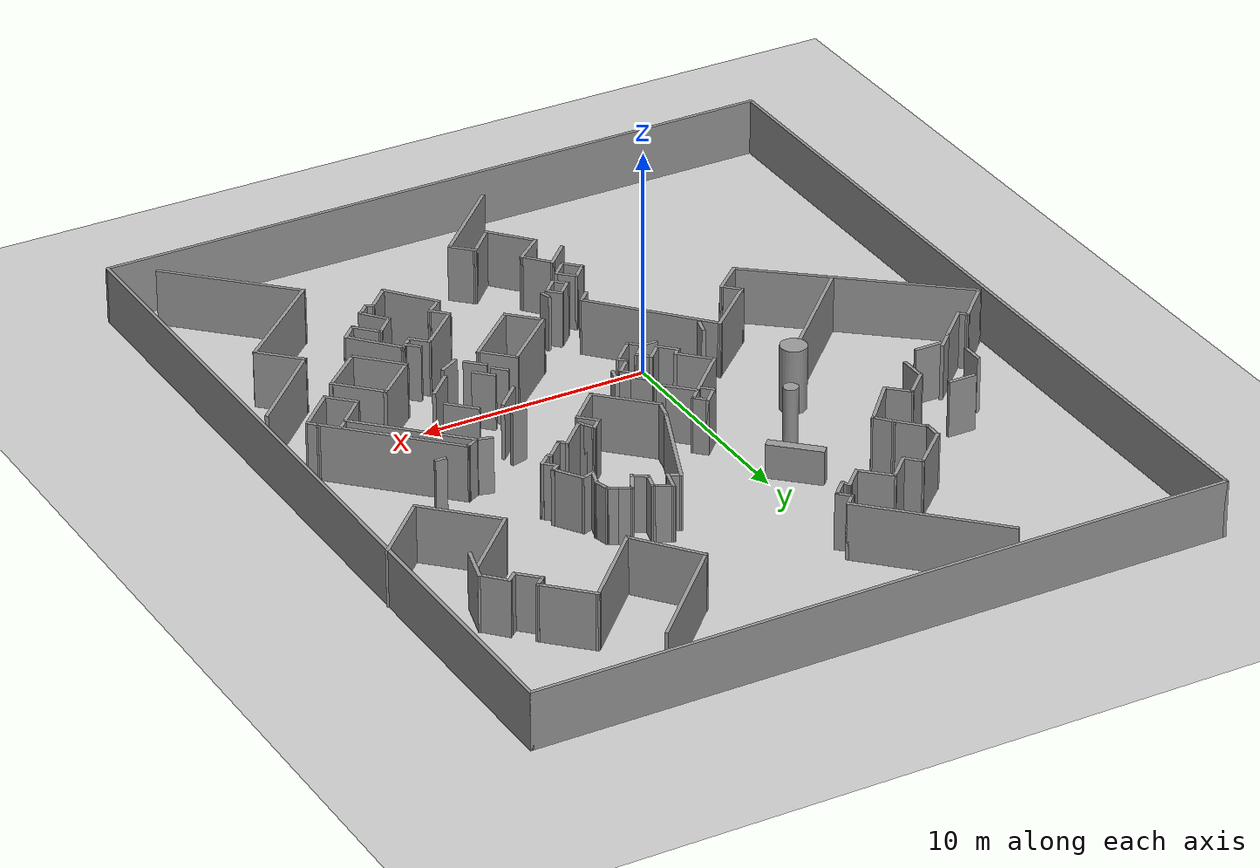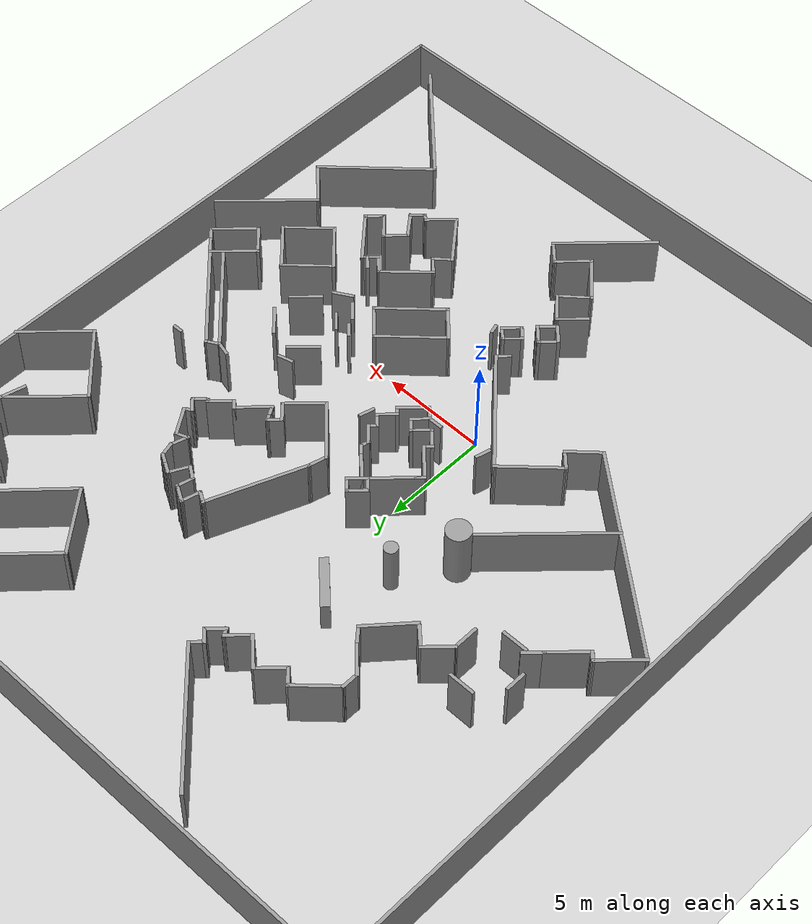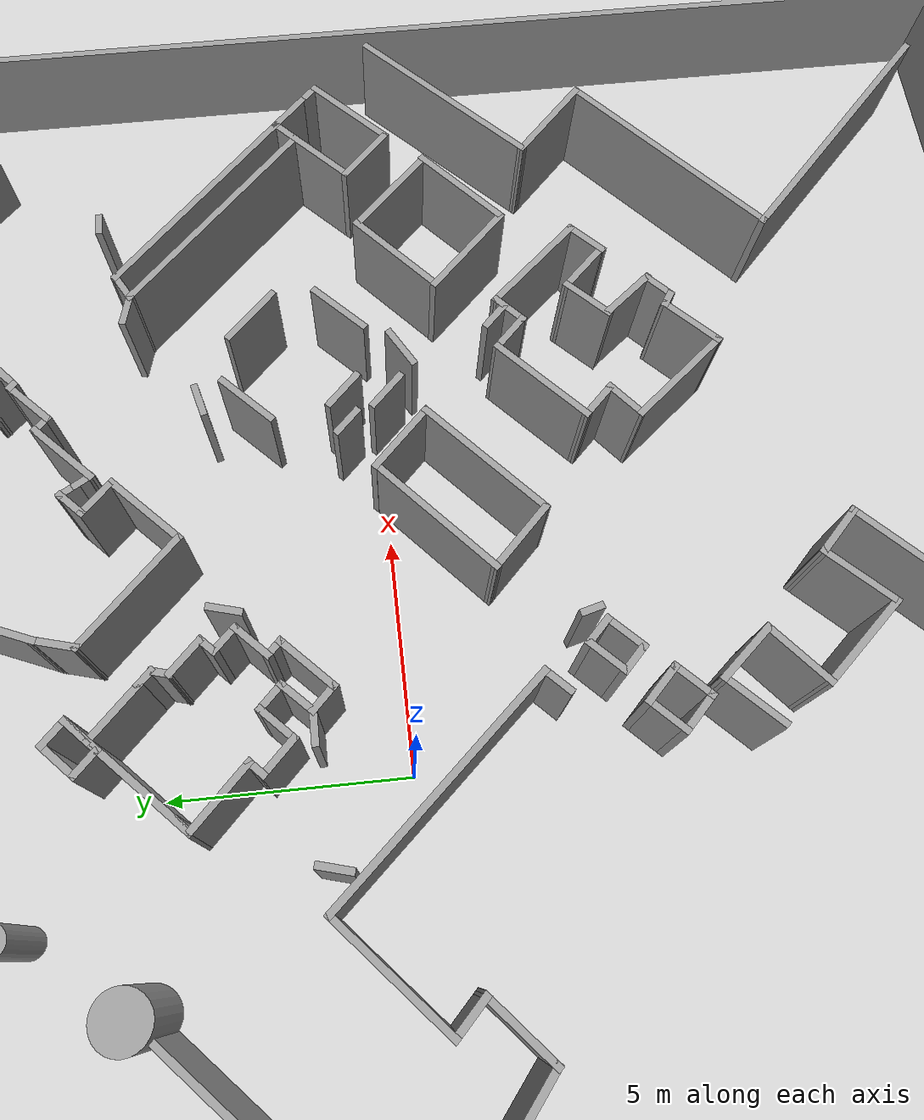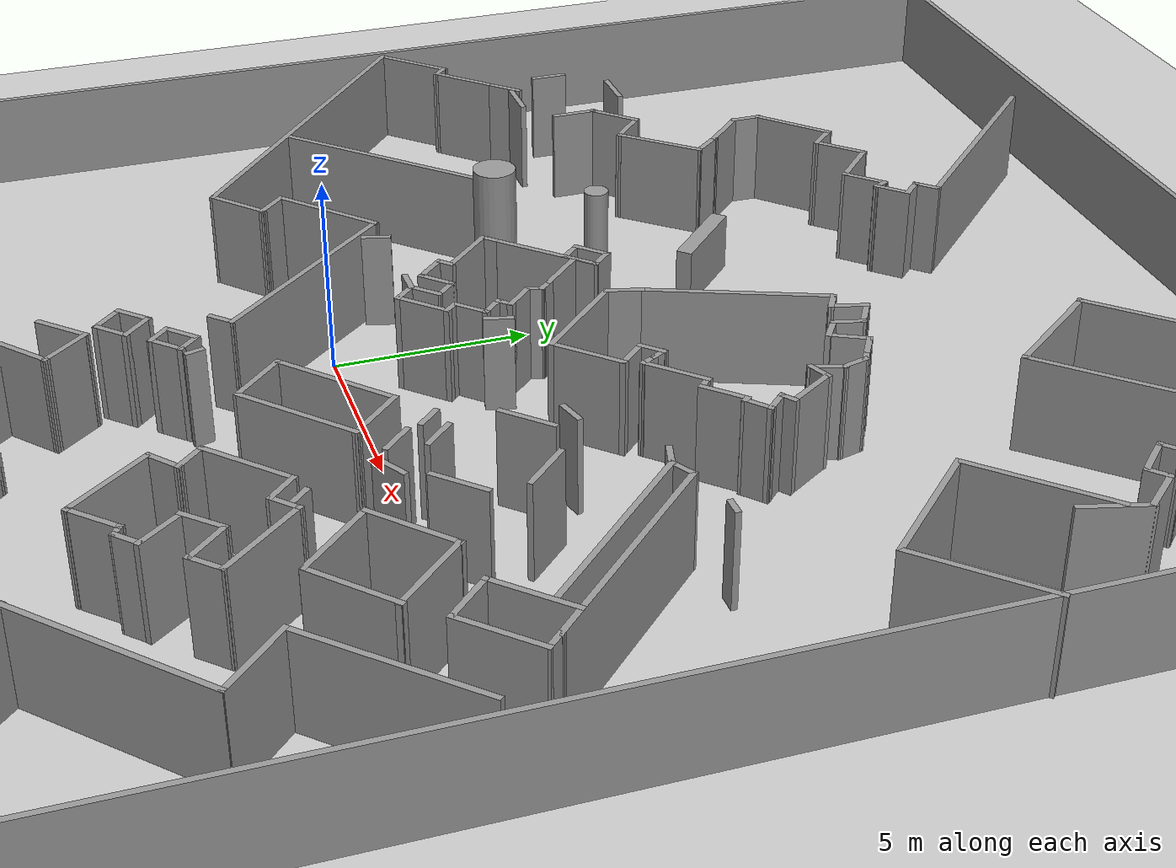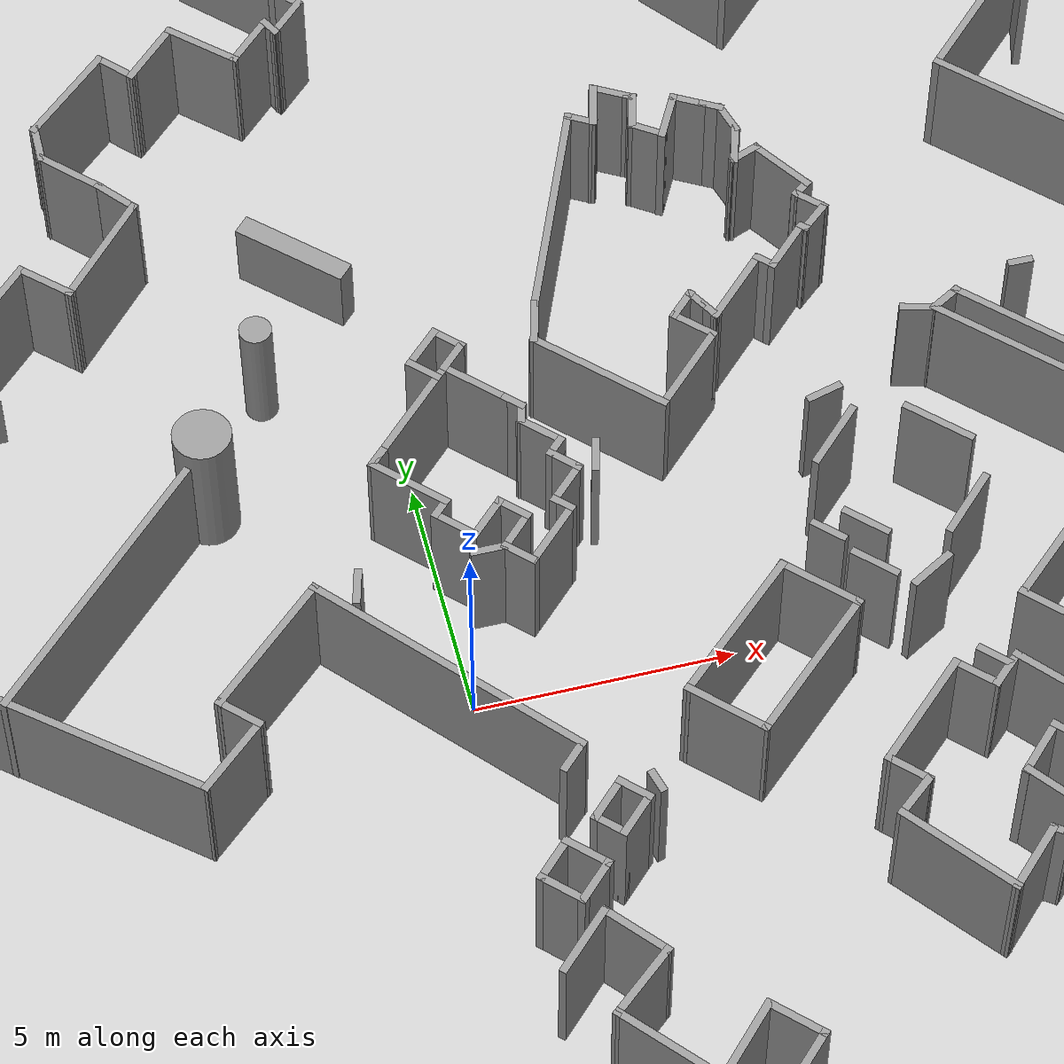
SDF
<sdf version="1.7">
 <world name="default">
  <light name="sun" type="directional">
   <pose>0 0 10 0 -0 0</pose>
   <diffuse>0.8 0.8 0.8 1</diffuse>
   <specular>0.2 0.2 0.2 1</specular>
   <attenuation>
    <range>1000</range>
    <constant>0.9</constant>
    <linear>0.01</linear>
    <quadratic>0.001</quadratic>
   </attenuation>
   <direction>-0.5 0.1 -0.9</direction>
   <spot><inner_angle>0</inner_angle><outer_angle>0</outer_angle><falloff>0</falloff></spot>
  </light>
  <model name="ground_plane">
   <static>1</static>
   <link name="link">
    <collision name="collision">
     <geometry><plane><normal>0 0 1</normal><size>100 100</size></plane></geometry>
     <surface>
      <contact><collide_bitmask>65535</collide_bitmask></contact>
      <friction><ode><mu>100</mu><mu2>50</mu2></ode></friction>
     </surface>
    </collision>
    <visual name="visual">
     <cast_shadows>0</cast_shadows>
     <geometry><plane><normal>0 0 1</normal><size>100 100</size></plane></geometry>
     <material>
      <script><uri>file://media/materials/scripts/gazebo.material</uri><name>Gazebo/Grey</name></script>
     </material>
    </visual>
   </link>
  </model>
  <gravity>0 0 -9.8</gravity>
  <magnetic_field>6e-06 2.3e-05 -4.2e-05</magnetic_field>
  <atmosphere type="adiabatic"/>
  <physics type="ode">
   <max_step_size>0.001</max_step_size>
   <real_time_factor>1</real_time_factor>
   <real_time_update_rate>1000</real_time_update_rate>
  </physics>
  <scene><ambient>0.4 0.4 0.4 1</ambient><background>0.7 0.7 0.7 1</background><shadows>1</shadows></scene>
  <spherical_coordinates>
   <surface_model>EARTH_WGS84</surface_model>
   <latitude_deg>0</latitude_deg>
   <longitude_deg>0</longitude_deg>
   <elevation>0</elevation>
   <heading_deg>0</heading_deg>
  </spherical_coordinates>
  <model name="grit_v2">
   <pose>1.8607 3.79365 0 0 -0 0</pose>
   <link name="Wall_1">
    <collision name="Wall_1_Collision">
     <geometry><box><size>36.5 0.15 2.5</size></box></geometry>
     <pose>0 0 1.25 0 -0 0</pose>
    </collision>
    <visual name="Wall_1_Visual">
     <pose>0 0 1.25 0 -0 0</pose>
     <geometry><box><size>36.5 0.15 2.5</size></box></geometry>
     <material>
      <script><uri>file://media/materials/scripts/gazebo.material</uri><name>Gazebo/Grey</name></script>
      <ambient>1 1 1 1</ambient>
     </material>
     <meta><layer>0</layer></meta>
    </visual>
    <pose>-15.2099 0 0 0 -0 1.5708</pose>
   </link>
   <link name="Wall_10">
    <collision name="Wall_10_Collision">
     <geometry><box><size>6.03502 0.15 2.5</size></box></geometry>
     <pose>0 0 1.25 0 -0 0</pose>
    </collision>
    <visual name="Wall_10_Visual">
     <pose>0 0 1.25 0 -0 0</pose>
     <geometry><box><size>6.03502 0.15 2.5</size></box></geometry>
     <material>
      <script><uri>file://media/materials/scripts/gazebo.material</uri><name>Gazebo/Grey</name></script>
      <ambient>1 1 1 1</ambient>
     </material>
     <meta><layer>0</layer></meta>
    </visual>
    <pose>-2.43335 -4.21243 0 0 -0 -0.841252</pose>
   </link>
   <link name="Wall_100">
    <collision name="Wall_100_Collision">
     <geometry><box><size>0.467184 0.15 2.5</size></box></geometry>
     <pose>0 0 1.25 0 -0 0</pose>
    </collision>
    <visual name="Wall_100_Visual">
     <pose>0 0 1.25 0 -0 0</pose>
     <geometry><box><size>0.467184 0.15 2.5</size></box></geometry>
     <material>
      <script><uri>file://media/materials/scripts/gazebo.material</uri><name>Gazebo/Grey</name></script>
      <ambient>1 1 1 1</ambient>
     </material>
     <meta><layer>0</layer></meta>
    </visual>
    <pose>-2.38111 11.1848 0 0 -0 2.06748</pose>
   </link>
   <link name="Wall_102">
    <collision name="Wall_102_Collision">
     <geometry><box><size>1.25 0.15 2.5</size></box></geometry>
     <pose>0 0 1.25 0 -0 0</pose>
    </collision>
    <visual name="Wall_102_Visual">
     <pose>0 0 1.25 0 -0 0</pose>
     <geometry><box><size>1.25 0.15 2.5</size></box></geometry>
     <material>
      <script><uri>file://media/materials/scripts/gazebo.material</uri><name>Gazebo/Grey</name></script>
      <ambient>1 1 1 1</ambient>
     </material>
     <meta><layer>0</layer></meta>
    </visual>
    <pose>-2.84559 10.9354 0 0 -0 0.785398</pose>
   </link>
   <link name="Wall_104">
    <collision name="Wall_104_Collision">
     <geometry><box><size>0.75 0.15 2.5</size></box></geometry>
     <pose>0 0 1.25 0 -0 0</pose>
    </collision>
    <visual name="Wall_104_Visual">
     <pose>0 0 1.25 0 -0 0</pose>
     <geometry><box><size>0.75 0.15 2.5</size></box></geometry>
     <material>
      <script><uri>file://media/materials/scripts/gazebo.material</uri><name>Gazebo/Grey</name></script>
      <ambient>1 1 1 1</ambient>
     </material>
     <meta><layer>0</layer></meta>
    </visual>
    <pose>-1.91663 11.8586 0 0 -0 2.35619</pose>
   </link>
   <link name="Wall_105">
    <collision name="Wall_105_Collision">
     <geometry><box><size>0.75 0.15 2.5</size></box></geometry>
     <pose>0 0 1.25 0 -0 0</pose>
    </collision>
    <visual name="Wall_105_Visual">
     <pose>0 0 1.25 0 -0 0</pose>
     <geometry><box><size>0.75 0.15 2.5</size></box></geometry>
     <material>
      <script><uri>file://media/materials/scripts/gazebo.material</uri><name>Gazebo/Grey</name></script>
      <ambient>1 1 1 1</ambient>
     </material>
     <meta><layer>0</layer></meta>
    </visual>
    <pose>-1.91663 12.2828 0 0 -0 0.785398</pose>
   </link>
   <link name="Wall_106">
    <collision name="Wall_106_Collision">
     <geometry><box><size>6.75 0.15 2.5</size></box></geometry>
     <pose>0 0 1.25 0 -0 0</pose>
    </collision>
    <visual name="Wall_106_Visual">
     <pose>0 0 1.25 0 -0 0</pose>
     <geometry><box><size>6.75 0.15 2.5</size></box></geometry>
     <material>
      <script><uri>file://media/materials/scripts/gazebo.material</uri><name>Gazebo/Grey</name></script>
      <ambient>1 1 1 1</ambient>
     </material>
     <meta><layer>0</layer></meta>
    </visual>
    <pose>-4.03795 14.8284 0 0 -0 2.35619</pose>
   </link>
   <link name="Wall_108">
    <collision name="Wall_108_Collision">
     <geometry><box><size>5.8158 0.15 2.5</size></box></geometry>
     <pose>0 0 1.25 0 -0 0</pose>
    </collision>
    <visual name="Wall_108_Visual">
     <pose>0 0 1.25 0 -0 0</pose>
     <geometry><box><size>5.8158 0.15 2.5</size></box></geometry>
     <material>
      <script><uri>file://media/materials/scripts/gazebo.material</uri><name>Gazebo/Grey</name></script>
      <ambient>1 1 1 1</ambient>
     </material>
     <meta><layer>0</layer></meta>
    </visual>
    <pose>6.8454 15.0408 0 0 -0 0.796946</pose>
   </link>
   <link name="Wall_111">
    <collision name="Wall_111_Collision">
     <geometry><box><size>4.31594 0.15 2.5</size></box></geometry>
     <pose>0 0 1.25 0 -0 0</pose>
    </collision>
    <visual name="Wall_111_Visual">
     <pose>0 0 1.25 0 -0 0</pose>
     <geometry><box><size>4.31594 0.15 2.5</size></box></geometry>
     <material>
      <script><uri>file://media/materials/scripts/gazebo.material</uri><name>Gazebo/Grey</name></script>
      <ambient>1 1 1 1</ambient>
     </material>
     <meta><layer>0</layer></meta>
    </visual>
    <pose>8.29293 11.9869 0 0 -0 0.801103</pose>
   </link>
   <link name="Wall_112">
    <collision name="Wall_112_Collision">
     <geometry><box><size>2.5 0.15 2.5</size></box></geometry>
     <pose>0 0 1.25 0 -0 0</pose>
    </collision>
    <visual name="Wall_112_Visual">
     <pose>0 0 1.25 0 -0 0</pose>
     <geometry><box><size>2.5 0.15 2.5</size></box></geometry>
     <material>
      <script><uri>file://media/materials/scripts/gazebo.material</uri><name>Gazebo/Grey</name></script>
      <ambient>1 1 1 1</ambient>
     </material>
     <meta><layer>0</layer></meta>
    </visual>
    <pose>10.5733 12.6519 0 0 -0 -0.785398</pose>
   </link>
   <link name="Wall_113">
    <collision name="Wall_113_Collision">
     <geometry><box><size>0.655092 0.15 2.5</size></box></geometry>
     <pose>0 0 1.25 0 -0 0</pose>
    </collision>
    <visual name="Wall_113_Visual">
     <pose>0 0 1.25 0 -0 0</pose>
     <geometry><box><size>0.655092 0.15 2.5</size></box></geometry>
     <material>
      <script><uri>file://media/materials/scripts/gazebo.material</uri><name>Gazebo/Grey</name></script>
      <ambient>1 1 1 1</ambient>
     </material>
     <meta><layer>0</layer></meta>
    </visual>
    <pose>11.2172 11.6513 0 0 -0 -2.40451</pose>
   </link>
   <link name="Wall_114">
    <collision name="Wall_114_Collision">
     <geometry><box><size>1.25 0.15 2.5</size></box></geometry>
     <pose>0 0 1.25 0 -0 0</pose>
    </collision>
    <visual name="Wall_114_Visual">
     <pose>0 0 1.25 0 -0 0</pose>
     <geometry><box><size>1.25 0.15 2.5</size></box></geometry>
     <material>
      <script><uri>file://media/materials/scripts/gazebo.material</uri><name>Gazebo/Grey</name></script>
      <ambient>1 1 1 1</ambient>
     </material>
     <meta><layer>0</layer></meta>
    </visual>
    <pose>11.4076 11.0926 0 0 -0 -0.785398</pose>
   </link>
   <link name="Wall_115">
    <collision name="Wall_115_Collision">
     <geometry><box><size>0.655092 0.15 2.5</size></box></geometry>
     <pose>0 0 1.25 0 -0 0</pose>
    </collision>
    <visual name="Wall_115_Visual">
     <pose>0 0 1.25 0 -0 0</pose>
     <geometry><box><size>0.655092 0.15 2.5</size></box></geometry>
     <material>
      <script><uri>file://media/materials/scripts/gazebo.material</uri><name>Gazebo/Grey</name></script>
      <ambient>1 1 1 1</ambient>
     </material>
     <meta><layer>0</layer></meta>
    </visual>
    <pose>11.995 10.8734 0 0 -0 0.737081</pose>
   </link>
   <link name="Wall_116">
    <collision name="Wall_116_Collision">
     <geometry><box><size>1.33207 0.15 2.5</size></box></geometry>
     <pose>0 0 1.25 0 -0 0</pose>
    </collision>
    <visual name="Wall_116_Visual">
     <pose>0 0 1.25 0 -0 0</pose>
     <geometry><box><size>1.33207 0.15 2.5</size></box></geometry>
     <material>
      <script><uri>file://media/materials/scripts/gazebo.material</uri><name>Gazebo/Grey</name></script>
      <ambient>1 1 1 1</ambient>
     </material>
     <meta><layer>0</layer></meta>
    </visual>
    <pose>12.5795 10.6058 0 0 -0 -0.833153</pose>
   </link>
   <link name="Wall_117">
    <collision name="Wall_117_Collision">
     <geometry><box><size>1.75 0.15 2.5</size></box></geometry>
     <pose>0 0 1.25 0 -0 0</pose>
    </collision>
    <visual name="Wall_117_Visual">
     <pose>0 0 1.25 0 -0 0</pose>
     <geometry><box><size>1.75 0.15 2.5</size></box></geometry>
     <material>
      <script><uri>file://media/materials/scripts/gazebo.material</uri><name>Gazebo/Grey</name></script>
      <ambient>1 1 1 1</ambient>
     </material>
     <meta><layer>0</layer></meta>
    </visual>
    <pose>12.7966 9.39565 0 0 -0 -1.8326</pose>
   </link>
   <link name="Wall_119">
    <collision name="Wall_119_Collision">
     <geometry><box><size>3.35633 0.15 2.5</size></box></geometry>
     <pose>0 0 1.25 0 -0 0</pose>
    </collision>
    <visual name="Wall_119_Visual">
     <pose>0 0 1.25 0 -0 0</pose>
     <geometry><box><size>3.35633 0.15 2.5</size></box></geometry>
     <material>
      <script><uri>file://media/materials/scripts/gazebo.material</uri><name>Gazebo/Grey</name></script>
      <ambient>1 1 1 1</ambient>
     </material>
     <meta><layer>0</layer></meta>
    </visual>
    <pose>5.85443 11.776 0 0 -0 -0.90605</pose>
   </link>
   <link name="Wall_12">
    <collision name="Wall_12_Collision">
     <geometry><box><size>1 0.15 2.5</size></box></geometry>
     <pose>0 0 1.25 0 -0 0</pose>
    </collision>
    <visual name="Wall_12_Visual">
     <pose>0 0 1.25 0 -0 0</pose>
     <geometry><box><size>1 0.15 2.5</size></box></geometry>
     <material>
      <script><uri>file://media/materials/scripts/gazebo.material</uri><name>Gazebo/Grey</name></script>
      <ambient>1 1 1 1</ambient>
     </material>
     <meta><layer>0</layer></meta>
    </visual>
    <pose>-6.26045 -4.30157 0 0 -0 -0.785398</pose>
   </link>
   <link name="Wall_121">
    <collision name="Wall_121_Collision">
     <geometry><box><size>3.75 0.15 2.5</size></box></geometry>
     <pose>0 0 1.25 0 -0 0</pose>
    </collision>
    <visual name="Wall_121_Visual">
     <pose>0 0 1.25 0 -0 0</pose>
     <geometry><box><size>3.75 0.15 2.5</size></box></geometry>
     <material>
      <script><uri>file://media/materials/scripts/gazebo.material</uri><name>Gazebo/Grey</name></script>
      <ambient>1 1 1 1</ambient>
     </material>
     <meta><layer>0</layer></meta>
    </visual>
    <pose>11.5372 5.81042 0 0 -0 2.35619</pose>
   </link>
   <link name="Wall_122">
    <collision name="Wall_122_Collision">
     <geometry><box><size>3.75 0.15 2.5</size></box></geometry>
     <pose>0 0 1.25 0 -0 0</pose>
    </collision>
    <visual name="Wall_122_Visual">
     <pose>0 0 1.25 0 -0 0</pose>
     <geometry><box><size>3.75 0.15 2.5</size></box></geometry>
     <material>
      <script><uri>file://media/materials/scripts/gazebo.material</uri><name>Gazebo/Grey</name></script>
      <ambient>1 1 1 1</ambient>
     </material>
     <meta><layer>0</layer></meta>
    </visual>
    <pose>11.5372 8.356 0 0 -0 0.785398</pose>
   </link>
   <link name="Wall_124">
    <collision name="Wall_124_Collision">
     <geometry><box><size>3.5 0.15 2.5</size></box></geometry>
     <pose>0 0 1.25 0 -0 0</pose>
    </collision>
    <visual name="Wall_124_Visual">
     <pose>0 0 1.25 0 -0 0</pose>
     <geometry><box><size>3.5 0.15 2.5</size></box></geometry>
     <material>
      <script><uri>file://media/materials/scripts/gazebo.material</uri><name>Gazebo/Grey</name></script>
      <ambient>1 1 1 1</ambient>
     </material>
     <meta><layer>0</layer></meta>
    </visual>
    <pose>13.9944 5.72203 0 0 -0 0.785398</pose>
   </link>
   <link name="Wall_126">
    <collision name="Wall_126_Collision">
     <geometry><box><size>0.5 0.15 2.5</size></box></geometry>
     <pose>0 0 1.25 0 -0 0</pose>
    </collision>
    <visual name="Wall_126_Visual">
     <pose>0 0 1.25 0 -0 0</pose>
     <geometry><box><size>0.5 0.15 2.5</size></box></geometry>
     <material>
      <script><uri>file://media/materials/scripts/gazebo.material</uri><name>Gazebo/Grey</name></script>
      <ambient>1 1 1 1</ambient>
     </material>
     <meta><layer>0</layer></meta>
    </visual>
    <pose>-2.63002 0.497043 0 0 -0 -2.35619</pose>
   </link>
   <link name="Wall_127">
    <collision name="Wall_127_Collision">
     <geometry><box><size>1.75 0.15 2.5</size></box></geometry>
     <pose>0 0 1.25 0 -0 0</pose>
    </collision>
    <visual name="Wall_127_Visual">
     <pose>0 0 1.25 0 -0 0</pose>
     <geometry><box><size>1.75 0.15 2.5</size></box></geometry>
     <material>
      <script><uri>file://media/materials/scripts/gazebo.material</uri><name>Gazebo/Grey</name></script>
      <ambient>1 1 1 1</ambient>
     </material>
     <meta><layer>0</layer></meta>
    </visual>
    <pose>-2.18808 -0.192386 0 0 -0 -0.785398</pose>
   </link>
   <link name="Wall_128">
    <collision name="Wall_128_Collision">
     <geometry><box><size>0.5 0.15 2.5</size></box></geometry>
     <pose>0 0 1.25 0 -0 0</pose>
    </collision>
    <visual name="Wall_128_Visual">
     <pose>0 0 1.25 0 -0 0</pose>
     <geometry><box><size>0.5 0.15 2.5</size></box></geometry>
     <material>
      <script><uri>file://media/materials/scripts/gazebo.material</uri><name>Gazebo/Grey</name></script>
      <ambient>1 1 1 1</ambient>
     </material>
     <meta><layer>0</layer></meta>
    </visual>
    <pose>-1.74613 -0.881815 0 0 -0 -2.35619</pose>
   </link>
   <link name="Wall_129">
    <collision name="Wall_129_Collision">
     <geometry><box><size>1 0.15 2.5</size></box></geometry>
     <pose>0 0 1.25 0 -0 0</pose>
    </collision>
    <visual name="Wall_129_Visual">
     <pose>0 0 1.25 0 -0 0</pose>
     <geometry><box><size>1 0.15 2.5</size></box></geometry>
     <material>
      <script><uri>file://media/materials/scripts/gazebo.material</uri><name>Gazebo/Grey</name></script>
      <ambient>1 1 1 1</ambient>
     </material>
     <meta><layer>0</layer></meta>
    </visual>
    <pose>-1.56936 -1.30608 0 0 -0 -0.785398</pose>
   </link>
   <link name="Wall_130">
    <collision name="Wall_130_Collision">
     <geometry><box><size>1 0.15 2.5</size></box></geometry>
     <pose>0 0 1.25 0 -0 0</pose>
    </collision>
    <visual name="Wall_130_Visual">
     <pose>0 0 1.25 0 -0 0</pose>
     <geometry><box><size>1 0.15 2.5</size></box></geometry>
     <material>
      <script><uri>file://media/materials/scripts/gazebo.material</uri><name>Gazebo/Grey</name></script>
      <ambient>1 1 1 1</ambient>
     </material>
     <meta><layer>0</layer></meta>
    </visual>
    <pose>-0.968317 -1.30608 0 0 -0 0.785398</pose>
   </link>
   <link name="Wall_131">
    <collision name="Wall_131_Collision">
     <geometry><box><size>0.75 0.15 2.5</size></box></geometry>
     <pose>0 0 1.25 0 -0 0</pose>
    </collision>
    <visual name="Wall_131_Visual">
     <pose>0 0 1.25 0 -0 0</pose>
     <geometry><box><size>0.75 0.15 2.5</size></box></geometry>
     <material>
      <script><uri>file://media/materials/scripts/gazebo.material</uri><name>Gazebo/Grey</name></script>
      <ambient>1 1 1 1</ambient>
     </material>
     <meta><layer>0</layer></meta>
    </visual>
    <pose>-0.455665 -1.21769 0 0 -0 -0.785398</pose>
   </link>
   <link name="Wall_132">
    <collision name="Wall_132_Collision">
     <geometry><box><size>0.931571 0.15 2.5</size></box></geometry>
     <pose>0 0 1.25 0 -0 0</pose>
    </collision>
    <visual name="Wall_132_Visual">
     <pose>0 0 1.25 0 -0 0</pose>
     <geometry><box><size>0.931571 0.15 2.5</size></box></geometry>
     <material>
      <script><uri>file://media/materials/scripts/gazebo.material</uri><name>Gazebo/Grey</name></script>
      <ambient>1 1 1 1</ambient>
     </material>
     <meta><layer>0</layer></meta>
    </visual>
    <pose>-0.516485 -1.70948 0 0 -0 -2.34405</pose>
   </link>
   <link name="Wall_133">
    <collision name="Wall_133_Collision">
     <geometry><box><size>0.75 0.15 2.5</size></box></geometry>
     <pose>0 0 1.25 0 -0 0</pose>
    </collision>
    <visual name="Wall_133_Visual">
     <pose>0 0 1.25 0 -0 0</pose>
     <geometry><box><size>0.75 0.15 2.5</size></box></geometry>
     <material>
      <script><uri>file://media/materials/scripts/gazebo.material</uri><name>Gazebo/Grey</name></script>
      <ambient>1 1 1 1</ambient>
     </material>
     <meta><layer>0</layer></meta>
    </visual>
    <pose>-0.577305 -2.20128 0 0 -0 -0.785398</pose>
   </link>
   <link name="Wall_134">
    <collision name="Wall_134_Collision">
     <geometry><box><size>1.5 0.15 2.5</size></box></geometry>
     <pose>0 0 1.25 0 -0 0</pose>
    </collision>
    <visual name="Wall_134_Visual">
     <pose>0 0 1.25 0 -0 0</pose>
     <geometry><box><size>1.5 0.15 2.5</size></box></geometry>
     <material>
      <script><uri>file://media/materials/scripts/gazebo.material</uri><name>Gazebo/Grey</name></script>
      <ambient>1 1 1 1</ambient>
     </material>
     <meta><layer>0</layer></meta>
    </visual>
    <pose>0.112124 -1.93611 0 0 -0 0.785398</pose>
   </link>
   <link name="Wall_135">
    <collision name="Wall_135_Collision">
     <geometry><box><size>0.5 0.15 2.5</size></box></geometry>
     <pose>0 0 1.25 0 -0 0</pose>
    </collision>
    <visual name="Wall_135_Visual">
     <pose>0 0 1.25 0 -0 0</pose>
     <geometry><box><size>0.5 0.15 2.5</size></box></geometry>
     <material>
      <script><uri>file://media/materials/scripts/gazebo.material</uri><name>Gazebo/Grey</name></script>
      <ambient>1 1 1 1</ambient>
     </material>
     <meta><layer>0</layer></meta>
    </visual>
    <pose>0.465678 -1.33507 0 0 -0 2.35619</pose>
   </link>
   <link name="Wall_136">
    <collision name="Wall_136_Collision">
     <geometry><box><size>1 0.15 2.5</size></box></geometry>
     <pose>0 0 1.25 0 -0 0</pose>
    </collision>
    <visual name="Wall_136_Visual">
     <pose>0 0 1.25 0 -0 0</pose>
     <geometry><box><size>1 0.15 2.5</size></box></geometry>
     <material>
      <script><uri>file://media/materials/scripts/gazebo.material</uri><name>Gazebo/Grey</name></script>
      <ambient>1 1 1 1</ambient>
     </material>
     <meta><layer>0</layer></meta>
    </visual>
    <pose>0.642454 -0.910808 0 0 -0 0.785398</pose>
   </link>
   <link name="Wall_137">
    <collision name="Wall_137_Collision">
     <geometry><box><size>0.75 0.15 2.5</size></box></geometry>
     <pose>0 0 1.25 0 -0 0</pose>
    </collision>
    <visual name="Wall_137_Visual">
     <pose>0 0 1.25 0 -0 0</pose>
     <geometry><box><size>0.75 0.15 2.5</size></box></geometry>
     <material>
      <script><uri>file://media/materials/scripts/gazebo.material</uri><name>Gazebo/Grey</name></script>
      <ambient>1 1 1 1</ambient>
     </material>
     <meta><layer>0</layer></meta>
    </visual>
    <pose>0.730843 -0.398156 0 0 -0 2.35619</pose>
   </link>
   <link name="Wall_138">
    <collision name="Wall_138_Collision">
     <geometry><box><size>0.5 0.15 2.5</size></box></geometry>
     <pose>0 0 1.25 0 -0 0</pose>
    </collision>
    <visual name="Wall_138_Visual">
     <pose>0 0 1.25 0 -0 0</pose>
     <geometry><box><size>0.5 0.15 2.5</size></box></geometry>
     <material>
      <script><uri>file://media/materials/scripts/gazebo.material</uri><name>Gazebo/Grey</name></script>
      <ambient>1 1 1 1</ambient>
     </material>
     <meta><layer>0</layer></meta>
    </visual>
    <pose>0.642454 -0.06228 0 0 -0 0.785398</pose>
   </link>
   <link name="Wall_139">
    <collision name="Wall_139_Collision">
     <geometry><box><size>1 0.15 2.5</size></box></geometry>
     <pose>0 0 1.25 0 -0 0</pose>
    </collision>
    <visual name="Wall_139_Visual">
     <pose>0 0 1.25 0 -0 0</pose>
     <geometry><box><size>1 0.15 2.5</size></box></geometry>
     <material>
      <script><uri>file://media/materials/scripts/gazebo.material</uri><name>Gazebo/Grey</name></script>
      <ambient>1 1 1 1</ambient>
     </material>
     <meta><layer>0</layer></meta>
    </visual>
    <pose>0.465678 0.361984 0 0 -0 2.35619</pose>
   </link>
   <link name="Wall_14">
    <collision name="Wall_14_Collision">
     <geometry><box><size>1.74495 0.15 2.5</size></box></geometry>
     <pose>0 0 1.25 0 -0 0</pose>
    </collision>
    <visual name="Wall_14_Visual">
     <pose>0 0 1.25 0 -0 0</pose>
     <geometry><box><size>1.74495 0.15 2.5</size></box></geometry>
     <material>
      <script><uri>file://media/materials/scripts/gazebo.material</uri><name>Gazebo/Grey</name></script>
      <ambient>1 1 1 1</ambient>
     </material>
     <meta><layer>0</layer></meta>
    </visual>
    <pose>-6.5537 -5.13444 0 0 -0 0.730911</pose>
   </link>
   <link name="Wall_140">
    <collision name="Wall_140_Collision">
     <geometry><box><size>0.5 0.15 2.5</size></box></geometry>
     <pose>0 0 1.25 0 -0 0</pose>
    </collision>
    <visual name="Wall_140_Visual">
     <pose>0 0 1.25 0 -0 0</pose>
     <geometry><box><size>0.5 0.15 2.5</size></box></geometry>
     <material>
      <script><uri>file://media/materials/scripts/gazebo.material</uri><name>Gazebo/Grey</name></script>
      <ambient>1 1 1 1</ambient>
     </material>
     <meta><layer>0</layer></meta>
    </visual>
    <pose>0.210451 0.831542 0 0 -0 1.309</pose>
   </link>
   <link name="Wall_141">
    <collision name="Wall_141_Collision">
     <geometry><box><size>0.5 0.15 2.5</size></box></geometry>
     <pose>0 0 1.25 0 -0 0</pose>
    </collision>
    <visual name="Wall_141_Visual">
     <pose>0 0 1.25 0 -0 0</pose>
     <geometry><box><size>0.5 0.15 2.5</size></box></geometry>
     <material>
      <script><uri>file://media/materials/scripts/gazebo.material</uri><name>Gazebo/Grey</name></script>
      <ambient>1 1 1 1</ambient>
     </material>
     <meta><layer>0</layer></meta>
    </visual>
    <pose>0.132 1.12432 0 0 -0 2.35619</pose>
   </link>
   <link name="Wall_142">
    <collision name="Wall_142_Collision">
     <geometry><box><size>1.5 0.15 2.5</size></box></geometry>
     <pose>0 0 1.25 0 -0 0</pose>
    </collision>
    <visual name="Wall_142_Visual">
     <pose>0 0 1.25 0 -0 0</pose>
     <geometry><box><size>1.5 0.15 2.5</size></box></geometry>
     <material>
      <script><uri>file://media/materials/scripts/gazebo.material</uri><name>Gazebo/Grey</name></script>
      <ambient>1 1 1 1</ambient>
     </material>
     <meta><layer>0</layer></meta>
    </visual>
    <pose>-0.469041 1.72536 0 0 -0 2.35619</pose>
   </link>
   <link name="Wall_143">
    <collision name="Wall_143_Collision">
     <geometry><box><size>0.75 0.15 2.5</size></box></geometry>
     <pose>0 0 1.25 0 -0 0</pose>
    </collision>
    <visual name="Wall_143_Visual">
     <pose>0 0 1.25 0 -0 0</pose>
     <geometry><box><size>0.75 0.15 2.5</size></box></geometry>
     <material>
      <script><uri>file://media/materials/scripts/gazebo.material</uri><name>Gazebo/Grey</name></script>
      <ambient>1 1 1 1</ambient>
     </material>
     <meta><layer>0</layer></meta>
    </visual>
    <pose>-0.734206 2.41479 0 0 -0 0.785398</pose>
   </link>
   <link name="Wall_144">
    <collision name="Wall_144_Collision">
     <geometry><box><size>0.75 0.15 2.5</size></box></geometry>
     <pose>0 0 1.25 0 -0 0</pose>
    </collision>
    <visual name="Wall_144_Visual">
     <pose>0 0 1.25 0 -0 0</pose>
     <geometry><box><size>0.75 0.15 2.5</size></box></geometry>
     <material>
      <script><uri>file://media/materials/scripts/gazebo.material</uri><name>Gazebo/Grey</name></script>
      <ambient>1 1 1 1</ambient>
     </material>
     <meta><layer>0</layer></meta>
    </visual>
    <pose>-0.734206 2.83906 0 0 -0 2.35619</pose>
   </link>
   <link name="Wall_145">
    <collision name="Wall_145_Collision">
     <geometry><box><size>1 0.15 2.5</size></box></geometry>
     <pose>0 0 1.25 0 -0 0</pose>
    </collision>
    <visual name="Wall_145_Visual">
     <pose>0 0 1.25 0 -0 0</pose>
     <geometry><box><size>1 0.15 2.5</size></box></geometry>
     <material>
      <script><uri>file://media/materials/scripts/gazebo.material</uri><name>Gazebo/Grey</name></script>
      <ambient>1 1 1 1</ambient>
     </material>
     <meta><layer>0</layer></meta>
    </visual>
    <pose>-1.24686 2.75067 0 0 -0 -2.35619</pose>
   </link>
   <link name="Wall_146">
    <collision name="Wall_146_Collision">
     <geometry><box><size>0.75 0.15 2.5</size></box></geometry>
     <pose>0 0 1.25 0 -0 0</pose>
    </collision>
    <visual name="Wall_146_Visual">
     <pose>0 0 1.25 0 -0 0</pose>
     <geometry><box><size>0.75 0.15 2.5</size></box></geometry>
     <material>
      <script><uri>file://media/materials/scripts/gazebo.material</uri><name>Gazebo/Grey</name></script>
      <ambient>1 1 1 1</ambient>
     </material>
     <meta><layer>0</layer></meta>
    </visual>
    <pose>-1.33525 2.23801 0 0 -0 -0.785398</pose>
   </link>
   <link name="Wall_147">
    <collision name="Wall_147_Collision">
     <geometry><box><size>1 0.15 2.5</size></box></geometry>
     <pose>0 0 1.25 0 -0 0</pose>
    </collision>
    <visual name="Wall_147_Visual">
     <pose>0 0 1.25 0 -0 0</pose>
     <geometry><box><size>1 0.15 2.5</size></box></geometry>
     <material>
      <script><uri>file://media/materials/scripts/gazebo.material</uri><name>Gazebo/Grey</name></script>
      <ambient>1 1 1 1</ambient>
     </material>
     <meta><layer>0</layer></meta>
    </visual>
    <pose>-0.822594 2.3264 0 0 -0 0.785398</pose>
   </link>
   <link name="Wall_148">
    <collision name="Wall_148_Collision">
     <geometry><box><size>3.32163 0.15 2.5</size></box></geometry>
     <pose>0 0 1.25 0 -0 0</pose>
    </collision>
    <visual name="Wall_148_Visual">
     <pose>0 0 1.25 0 -0 0</pose>
     <geometry><box><size>3.32163 0.15 2.5</size></box></geometry>
     <material>
      <script><uri>file://media/materials/scripts/gazebo.material</uri><name>Gazebo/Grey</name></script>
      <ambient>1 1 1 1</ambient>
     </material>
     <meta><layer>0</layer></meta>
    </visual>
    <pose>-1.63792 1.50011 0 0 -0 -2.3513</pose>
   </link>
   <link name="Wall_150">
    <collision name="Wall_150_Collision">
     <geometry><box><size>0.75 0.15 2.5</size></box></geometry>
     <pose>0 0 1.25 0 -0 0</pose>
    </collision>
    <visual name="Wall_150_Visual">
     <pose>0 0 1.25 0 -0 0</pose>
     <geometry><box><size>0.75 0.15 2.5</size></box></geometry>
     <material>
      <script><uri>file://media/materials/scripts/gazebo.material</uri><name>Gazebo/Grey</name></script>
      <ambient>1 1 1 1</ambient>
     </material>
     <meta><layer>0</layer></meta>
    </visual>
    <pose>1.32504 -0.41635 0 0 -0 1.309</pose>
   </link>
   <link name="Wall_152">
    <collision name="Wall_152_Collision">
     <geometry><box><size>0.75 0.15 2.5</size></box></geometry>
     <pose>0 0 1.25 0 -0 0</pose>
    </collision>
    <visual name="Wall_152_Visual">
     <pose>0 0 1.25 0 -0 0</pose>
     <geometry><box><size>0.75 0.15 2.5</size></box></geometry>
     <material>
      <script><uri>file://media/materials/scripts/gazebo.material</uri><name>Gazebo/Grey</name></script>
      <ambient>1 1 1 1</ambient>
     </material>
     <meta><layer>0</layer></meta>
    </visual>
    <pose>5.84152 -0.089352 0 0 -0 0.261799</pose>
   </link>
   <link name="Wall_154">
    <collision name="Wall_154_Collision">
     <geometry><box><size>0.75 0.15 2.5</size></box></geometry>
     <pose>0 0 1.25 0 -0 0</pose>
    </collision>
    <visual name="Wall_154_Visual">
     <pose>0 0 1.25 0 -0 0</pose>
     <geometry><box><size>0.75 0.15 2.5</size></box></geometry>
     <material>
      <script><uri>file://media/materials/scripts/gazebo.material</uri><name>Gazebo/Grey</name></script>
      <ambient>1 1 1 1</ambient>
     </material>
     <meta><layer>0</layer></meta>
    </visual>
    <pose>8.14255 1.37921 0 0 -0 -0.261799</pose>
   </link>
   <link name="Wall_156">
    <collision name="Wall_156_Collision">
     <geometry><box><size>2 0.15 2.5</size></box></geometry>
     <pose>0 0 1.25 0 -0 0</pose>
    </collision>
    <visual name="Wall_156_Visual">
     <pose>0 0 1.25 0 -0 0</pose>
     <geometry><box><size>2 0.15 2.5</size></box></geometry>
     <material>
      <script><uri>file://media/materials/scripts/gazebo.material</uri><name>Gazebo/Grey</name></script>
      <ambient>1 1 1 1</ambient>
     </material>
     <meta><layer>0</layer></meta>
    </visual>
    <pose>3.52231 1.06719 0 0 -0 0.785398</pose>
   </link>
   <link name="Wall_157">
    <collision name="Wall_157_Collision">
     <geometry><box><size>1 0.15 2.5</size></box></geometry>
     <pose>0 0 1.25 0 -0 0</pose>
    </collision>
    <visual name="Wall_157_Visual">
     <pose>0 0 1.25 0 -0 0</pose>
     <geometry><box><size>1 0.15 2.5</size></box></geometry>
     <material>
      <script><uri>file://media/materials/scripts/gazebo.material</uri><name>Gazebo/Grey</name></script>
      <ambient>1 1 1 1</ambient>
     </material>
     <meta><layer>0</layer></meta>
    </visual>
    <pose>3.87586 2.02178 0 0 -0 2.35619</pose>
   </link>
   <link name="Wall_158">
    <collision name="Wall_158_Collision">
     <geometry><box><size>0.75 0.15 2.5</size></box></geometry>
     <pose>0 0 1.25 0 -0 0</pose>
    </collision>
    <visual name="Wall_158_Visual">
     <pose>0 0 1.25 0 -0 0</pose>
     <geometry><box><size>0.75 0.15 2.5</size></box></geometry>
     <material>
      <script><uri>file://media/materials/scripts/gazebo.material</uri><name>Gazebo/Grey</name></script>
      <ambient>1 1 1 1</ambient>
     </material>
     <meta><layer>0</layer></meta>
    </visual>
    <pose>3.78747 2.53444 0 0 -0 0.785398</pose>
   </link>
   <link name="Wall_159">
    <collision name="Wall_159_Collision">
     <geometry><box><size>0.5 0.15 2.5</size></box></geometry>
     <pose>0 0 1.25 0 -0 0</pose>
    </collision>
    <visual name="Wall_159_Visual">
     <pose>0 0 1.25 0 -0 0</pose>
     <geometry><box><size>0.5 0.15 2.5</size></box></geometry>
     <material>
      <script><uri>file://media/materials/scripts/gazebo.material</uri><name>Gazebo/Grey</name></script>
      <ambient>1 1 1 1</ambient>
     </material>
     <meta><layer>0</layer></meta>
    </visual>
    <pose>4.08711 2.59502 0 0 -0 -1.0472</pose>
   </link>
   <link name="Wall_16">
    <collision name="Wall_16_Collision">
     <geometry><box><size>3.08635 0.15 2.5</size></box></geometry>
     <pose>0 0 1.25 0 -0 0</pose>
    </collision>
    <visual name="Wall_16_Visual">
     <pose>0 0 1.25 0 -0 0</pose>
     <geometry><box><size>3.08635 0.15 2.5</size></box></geometry>
     <material>
      <script><uri>file://media/materials/scripts/gazebo.material</uri><name>Gazebo/Grey</name></script>
      <ambient>1 1 1 1</ambient>
     </material>
     <meta><layer>0</layer></meta>
    </visual>
    <pose>-5.4778 -3.00995 0 0 -0 -2.40056</pose>
   </link>
   <link name="Wall_161">
    <collision name="Wall_161_Collision">
     <geometry><box><size>0.5 0.15 2.5</size></box></geometry>
     <pose>0 0 1.25 0 -0 0</pose>
    </collision>
    <visual name="Wall_161_Visual">
     <pose>0 0 1.25 0 -0 0</pose>
     <geometry><box><size>0.5 0.15 2.5</size></box></geometry>
     <material>
      <script><uri>file://media/materials/scripts/gazebo.material</uri><name>Gazebo/Grey</name></script>
      <ambient>1 1 1 1</ambient>
     </material>
     <meta><layer>0</layer></meta>
    </visual>
    <pose>4.26211 2.29191 0 0 -0 -1.0472</pose>
   </link>
   <link name="Wall_162">
    <collision name="Wall_162_Collision">
     <geometry><box><size>1.75 0.15 2.5</size></box></geometry>
     <pose>0 0 1.25 0 -0 0</pose>
    </collision>
    <visual name="Wall_162_Visual">
     <pose>0 0 1.25 0 -0 0</pose>
     <geometry><box><size>1.75 0.15 2.5</size></box></geometry>
     <material>
      <script><uri>file://media/materials/scripts/gazebo.material</uri><name>Gazebo/Grey</name></script>
      <ambient>1 1 1 1</ambient>
     </material>
     <meta><layer>0</layer></meta>
    </visual>
    <pose>4.91529 2.70604 0 0 -0 0.785398</pose>
   </link>
   <link name="Wall_163">
    <collision name="Wall_163_Collision">
     <geometry><box><size>0.5 0.15 2.5</size></box></geometry>
     <pose>0 0 1.25 0 -0 0</pose>
    </collision>
    <visual name="Wall_163_Visual">
     <pose>0 0 1.25 0 -0 0</pose>
     <geometry><box><size>0.5 0.15 2.5</size></box></geometry>
     <material>
      <script><uri>file://media/materials/scripts/gazebo.material</uri><name>Gazebo/Grey</name></script>
      <ambient>1 1 1 1</ambient>
     </material>
     <meta><layer>0</layer></meta>
    </visual>
    <pose>5.60472 3.14798 0 0 -0 -0.785398</pose>
   </link>
   <link name="Wall_164">
    <collision name="Wall_164_Collision">
     <geometry><box><size>1.25 0.15 2.5</size></box></geometry>
     <pose>0 0 1.25 0 -0 0</pose>
    </collision>
    <visual name="Wall_164_Visual">
     <pose>0 0 1.25 0 -0 0</pose>
     <geometry><box><size>1.25 0.15 2.5</size></box></geometry>
     <material>
      <script><uri>file://media/materials/scripts/gazebo.material</uri><name>Gazebo/Grey</name></script>
      <ambient>1 1 1 1</ambient>
     </material>
     <meta><layer>0</layer></meta>
    </visual>
    <pose>6.11737 3.41314 0 0 -0 0.785398</pose>
   </link>
   <link name="Wall_165">
    <collision name="Wall_165_Collision">
     <geometry><box><size>0.25 0.15 2.5</size></box></geometry>
     <pose>0 0 1.25 0 -0 0</pose>
    </collision>
    <visual name="Wall_165_Visual">
     <pose>0 0 1.25 0 -0 0</pose>
     <geometry><box><size>0.25 0.15 2.5</size></box></geometry>
     <material>
      <script><uri>file://media/materials/scripts/gazebo.material</uri><name>Gazebo/Grey</name></script>
      <ambient>1 1 1 1</ambient>
     </material>
     <meta><layer>0</layer></meta>
    </visual>
    <pose>6.54164 3.7667 0 0 -0 -0.785398</pose>
   </link>
   <link name="Wall_166">
    <collision name="Wall_166_Collision">
     <geometry><box><size>0.790803 0.15 2.5</size></box></geometry>
     <pose>0 0 1.25 0 -0 0</pose>
    </collision>
    <visual name="Wall_166_Visual">
     <pose>0 0 1.25 0 -0 0</pose>
     <geometry><box><size>0.790803 0.15 2.5</size></box></geometry>
     <material>
      <script><uri>file://media/materials/scripts/gazebo.material</uri><name>Gazebo/Grey</name></script>
      <ambient>1 1 1 1</ambient>
     </material>
     <meta><layer>0</layer></meta>
    </visual>
    <pose>6.81855 3.94184 0 0 -0 0.716806</pose>
   </link>
   <link name="Wall_167">
    <collision name="Wall_167_Collision">
     <geometry><box><size>0.75 0.15 2.5</size></box></geometry>
     <pose>0 0 1.25 0 -0 0</pose>
    </collision>
    <visual name="Wall_167_Visual">
     <pose>0 0 1.25 0 -0 0</pose>
     <geometry><box><size>0.75 0.15 2.5</size></box></geometry>
     <material>
      <script><uri>file://media/materials/scripts/gazebo.material</uri><name>Gazebo/Grey</name></script>
      <ambient>1 1 1 1</ambient>
     </material>
     <meta><layer>0</layer></meta>
    </visual>
    <pose>6.84797 4.3612 0 0 -0 2.35619</pose>
   </link>
   <link name="Wall_168">
    <collision name="Wall_168_Collision">
     <geometry><box><size>0.489693 0.15 2.5</size></box></geometry>
     <pose>0 0 1.25 0 -0 0</pose>
    </collision>
    <visual name="Wall_168_Visual">
     <pose>0 0 1.25 0 -0 0</pose>
     <geometry><box><size>0.489693 0.15 2.5</size></box></geometry>
     <material>
      <script><uri>file://media/materials/scripts/gazebo.material</uri><name>Gazebo/Grey</name></script>
      <ambient>1 1 1 1</ambient>
     </material>
     <meta><layer>0</layer></meta>
    </visual>
    <pose>6.77364 4.67589 0 0 -0 0.62438</pose>
   </link>
   <link name="Wall_170">
    <collision name="Wall_170_Collision">
     <geometry><box><size>1.45475 0.15 2.5</size></box></geometry>
     <pose>0 0 1.25 0 -0 0</pose>
    </collision>
    <visual name="Wall_170_Visual">
     <pose>0 0 1.25 0 -0 0</pose>
     <geometry><box><size>1.45475 0.15 2.5</size></box></geometry>
     <material>
      <script><uri>file://media/materials/scripts/gazebo.material</uri><name>Gazebo/Grey</name></script>
      <ambient>1 1 1 1</ambient>
     </material>
     <meta><layer>0</layer></meta>
    </visual>
    <pose>6.54457 5.32044 0 0 -0 -0.989593</pose>
   </link>
   <link name="Wall_173">
    <collision name="Wall_173_Collision">
     <geometry><box><size>3 0.15 2.5</size></box></geometry>
     <pose>0 0 1.25 0 -0 0</pose>
    </collision>
    <visual name="Wall_173_Visual">
     <pose>0 0 1.25 0 -0 0</pose>
     <geometry><box><size>3 0.15 2.5</size></box></geometry>
     <material>
      <script><uri>file://media/materials/scripts/gazebo.material</uri><name>Gazebo/Grey</name></script>
      <ambient>1 1 1 1</ambient>
     </material>
     <meta><layer>0</layer></meta>
    </visual>
    <pose>1.86061 1.42074 0 0 -0 2.35619</pose>
   </link>
   <link name="Wall_174">
    <collision name="Wall_174_Collision">
     <geometry><box><size>1 0.15 2.5</size></box></geometry>
     <pose>0 0 1.25 0 -0 0</pose>
    </collision>
    <visual name="Wall_174_Visual">
     <pose>0 0 1.25 0 -0 0</pose>
     <geometry><box><size>1 0.15 2.5</size></box></geometry>
     <material>
      <script><uri>file://media/materials/scripts/gazebo.material</uri><name>Gazebo/Grey</name></script>
      <ambient>1 1 1 1</ambient>
     </material>
     <meta><layer>0</layer></meta>
    </visual>
    <pose>0.962979 2.83889 0 0 -0 1.309</pose>
   </link>
   <link name="Wall_176">
    <collision name="Wall_176_Collision">
     <geometry><box><size>0.658656 0.15 2.5</size></box></geometry>
     <pose>0 0 1.25 0 -0 0</pose>
    </collision>
    <visual name="Wall_176_Visual">
     <pose>0 0 1.25 0 -0 0</pose>
     <geometry><box><size>0.658656 0.15 2.5</size></box></geometry>
     <material>
      <script><uri>file://media/materials/scripts/gazebo.material</uri><name>Gazebo/Grey</name></script>
      <ambient>1 1 1 1</ambient>
     </material>
     <meta><layer>0</layer></meta>
    </visual>
    <pose>3.03264 7.38742 0 0 -0 -0.522795</pose>
   </link>
   <link name="Wall_177">
    <collision name="Wall_177_Collision">
     <geometry><box><size>1 0.15 2.5</size></box></geometry>
     <pose>0 0 1.25 0 -0 0</pose>
    </collision>
    <visual name="Wall_177_Visual">
     <pose>0 0 1.25 0 -0 0</pose>
     <geometry><box><size>1 0.15 2.5</size></box></geometry>
     <material>
      <script><uri>file://media/materials/scripts/gazebo.material</uri><name>Gazebo/Grey</name></script>
      <ambient>1 1 1 1</ambient>
     </material>
     <meta><layer>0</layer></meta>
    </visual>
    <pose>3.36299 7.67095 0 0 -0 1.309</pose>
   </link>
   <link name="Wall_178">
    <collision name="Wall_178_Collision">
     <geometry><box><size>0.841344 0.15 2.5</size></box></geometry>
     <pose>0 0 1.25 0 -0 0</pose>
    </collision>
    <visual name="Wall_178_Visual">
     <pose>0 0 1.25 0 -0 0</pose>
     <geometry><box><size>0.841344 0.15 2.5</size></box></geometry>
     <material>
      <script><uri>file://media/materials/scripts/gazebo.material</uri><name>Gazebo/Grey</name></script>
      <ambient>1 1 1 1</ambient>
     </material>
     <meta><layer>0</layer></meta>
    </visual>
    <pose>3.77225 7.90846 0 0 -0 -0.52419</pose>
   </link>
   <link name="Wall_18">
    <collision name="Wall_18_Collision">
     <geometry><box><size>2.25 0.15 2.5</size></box></geometry>
     <pose>0 0 1.25 0 -0 0</pose>
    </collision>
    <visual name="Wall_18_Visual">
     <pose>0 0 1.25 0 -0 0</pose>
     <geometry><box><size>2.25 0.15 2.5</size></box></geometry>
     <material>
      <script><uri>file://media/materials/scripts/gazebo.material</uri><name>Gazebo/Grey</name></script>
      <ambient>1 1 1 1</ambient>
     </material>
     <meta><layer>0</layer></meta>
    </visual>
    <pose>-14.1803 1.51258 0 0 -0 -2.35619</pose>
   </link>
   <link name="Wall_180">
    <collision name="Wall_180_Collision">
     <geometry><box><size>0.25 0.15 2.5</size></box></geometry>
     <pose>0 0 1.25 0 -0 0</pose>
    </collision>
    <visual name="Wall_180_Visual">
     <pose>0 0 1.25 0 -0 0</pose>
     <geometry><box><size>0.25 0.15 2.5</size></box></geometry>
     <material>
      <script><uri>file://media/materials/scripts/gazebo.material</uri><name>Gazebo/Grey</name></script>
      <ambient>1 1 1 1</ambient>
     </material>
     <meta><layer>0</layer></meta>
    </visual>
    <pose>4.11481 7.71044 0 0 -0 -0.523599</pose>
   </link>
   <link name="Wall_181">
    <collision name="Wall_181_Collision">
     <geometry><box><size>0.863143 0.15 2.5</size></box></geometry>
     <pose>0 0 1.25 0 -0 0</pose>
    </collision>
    <visual name="Wall_181_Visual">
     <pose>0 0 1.25 0 -0 0</pose>
     <geometry><box><size>0.863143 0.15 2.5</size></box></geometry>
     <material>
      <script><uri>file://media/materials/scripts/gazebo.material</uri><name>Gazebo/Grey</name></script>
      <ambient>1 1 1 1</ambient>
     </material>
     <meta><layer>0</layer></meta>
    </visual>
    <pose>4.0706 7.33978 0 0 -0 -1.81875</pose>
   </link>
   <link name="Wall_182">
    <collision name="Wall_182_Collision">
     <geometry><box><size>0.772525 0.15 2.5</size></box></geometry>
     <pose>0 0 1.25 0 -0 0</pose>
    </collision>
    <visual name="Wall_182_Visual">
     <pose>0 0 1.25 0 -0 0</pose>
     <geometry><box><size>0.772525 0.15 2.5</size></box></geometry>
     <material>
      <script><uri>file://media/materials/scripts/gazebo.material</uri><name>Gazebo/Grey</name></script>
      <ambient>1 1 1 1</ambient>
     </material>
     <meta><layer>0</layer></meta>
    </visual>
    <pose>4.23961 6.82438 0 0 -0 -0.602137</pose>
   </link>
   <link name="Wall_183">
    <collision name="Wall_183_Collision">
     <geometry><box><size>1.10745 0.15 2.5</size></box></geometry>
     <pose>0 0 1.25 0 -0 0</pose>
    </collision>
    <visual name="Wall_183_Visual">
     <pose>0 0 1.25 0 -0 0</pose>
     <geometry><box><size>1.10745 0.15 2.5</size></box></geometry>
     <material>
      <script><uri>file://media/materials/scripts/gazebo.material</uri><name>Gazebo/Grey</name></script>
      <ambient>1 1 1 1</ambient>
     </material>
     <meta><layer>0</layer></meta>
    </visual>
    <pose>4.71849 7.05888 0 0 -0 1.08774</pose>
   </link>
   <link name="Wall_185">
    <collision name="Wall_185_Collision">
     <geometry><box><size>0.75 0.15 2.5</size></box></geometry>
     <pose>0 0 1.25 0 -0 0</pose>
    </collision>
    <visual name="Wall_185_Visual">
     <pose>0 0 1.25 0 -0 0</pose>
     <geometry><box><size>0.75 0.15 2.5</size></box></geometry>
     <material>
      <script><uri>file://media/materials/scripts/gazebo.material</uri><name>Gazebo/Grey</name></script>
      <ambient>1 1 1 1</ambient>
     </material>
     <meta><layer>0</layer></meta>
    </visual>
    <pose>5.20066 7.33283 0 0 -0 -0.523599</pose>
   </link>
   <link name="Wall_186">
    <collision name="Wall_186_Collision">
     <geometry><box><size>0.5 0.15 2.5</size></box></geometry>
     <pose>0 0 1.25 0 -0 0</pose>
    </collision>
    <visual name="Wall_186_Visual">
     <pose>0 0 1.25 0 -0 0</pose>
     <geometry><box><size>0.5 0.15 2.5</size></box></geometry>
     <material>
      <script><uri>file://media/materials/scripts/gazebo.material</uri><name>Gazebo/Grey</name></script>
      <ambient>1 1 1 1</ambient>
     </material>
     <meta><layer>0</layer></meta>
    </visual>
    <pose>5.61203 7.09533 0 0 -0 -0.523599</pose>
   </link>
   <link name="Wall_187">
    <collision name="Wall_187_Collision">
     <geometry><box><size>0.75 0.15 2.5</size></box></geometry>
     <pose>0 0 1.25 0 -0 0</pose>
    </collision>
    <visual name="Wall_187_Visual">
     <pose>0 0 1.25 0 -0 0</pose>
     <geometry><box><size>0.75 0.15 2.5</size></box></geometry>
     <material>
      <script><uri>file://media/materials/scripts/gazebo.material</uri><name>Gazebo/Grey</name></script>
      <ambient>1 1 1 1</ambient>
     </material>
     <meta><layer>0</layer></meta>
    </visual>
    <pose>5.84123 6.71805 0 0 -0 -1.309</pose>
   </link>
   <link name="Wall_189">
    <collision name="Wall_189_Collision">
     <geometry><box><size>0.942471 0.15 2.5</size></box></geometry>
     <pose>0 0 1.25 0 -0 0</pose>
    </collision>
    <visual name="Wall_189_Visual">
     <pose>0 0 1.25 0 -0 0</pose>
     <geometry><box><size>0.942471 0.15 2.5</size></box></geometry>
     <material>
      <script><uri>file://media/materials/scripts/gazebo.material</uri><name>Gazebo/Grey</name></script>
      <ambient>1 1 1 1</ambient>
     </material>
     <meta><layer>0</layer></meta>
    </visual>
    <pose>5.80248 6.04952 0 0 -0 1.27266</pose>
   </link>
   <link name="Wall_19">
    <collision name="Wall_19_Collision">
     <geometry><box><size>10.2472 0.15 2.5</size></box></geometry>
     <pose>0 0 1.25 0 -0 0</pose>
    </collision>
    <visual name="Wall_19_Visual">
     <pose>0 0 1.25 0 -0 0</pose>
     <geometry><box><size>10.2472 0.15 2.5</size></box></geometry>
     <material>
      <script><uri>file://media/materials/scripts/gazebo.material</uri><name>Gazebo/Grey</name></script>
      <ambient>1 1 1 1</ambient>
     </material>
     <meta><layer>0</layer></meta>
    </visual>
    <pose>-11.0351 -2.44585 0 0 -0 -0.691883</pose>
   </link>
   <link name="Wall_191">
    <collision name="Wall_191_Collision">
     <geometry><box><size>0.686935 0.15 2.5</size></box></geometry>
     <pose>0 0 1.25 0 -0 0</pose>
    </collision>
    <visual name="Wall_191_Visual">
     <pose>0 0 1.25 0 -0 0</pose>
     <geometry><box><size>0.686935 0.15 2.5</size></box></geometry>
     <material>
      <script><uri>file://media/materials/scripts/gazebo.material</uri><name>Gazebo/Grey</name></script>
      <ambient>1 1 1 1</ambient>
     </material>
     <meta><layer>0</layer></meta>
    </visual>
    <pose>5.93625 5.78335 0 0 -0 0.37153</pose>
   </link>
   <link name="Wall_193">
    <collision name="Wall_193_Collision">
     <geometry><box><size>4.75601 0.15 2.5</size></box></geometry>
     <pose>0 0 1.25 0 -0 0</pose>
    </collision>
    <visual name="Wall_193_Visual">
     <pose>0 0 1.25 0 -0 0</pose>
     <geometry><box><size>4.75601 0.15 2.5</size></box></geometry>
     <material>
      <script><uri>file://media/materials/scripts/gazebo.material</uri><name>Gazebo/Grey</name></script>
      <ambient>1 1 1 1</ambient>
     </material>
     <meta><layer>0</layer></meta>
    </visual>
    <pose>1.94263 5.38191 0 0 -0 1.18358</pose>
   </link>
   <link name="Wall_195">
    <collision name="Wall_195_Collision">
     <geometry><box><size>1 0.15 2.5</size></box></geometry>
     <pose>0 0 1.25 0 -0 0</pose>
    </collision>
    <visual name="Wall_195_Visual">
     <pose>0 0 1.25 0 -0 0</pose>
     <geometry><box><size>1 0.15 2.5</size></box></geometry>
     <material>
      <script><uri>file://media/materials/scripts/gazebo.material</uri><name>Gazebo/Grey</name></script>
      <ambient>1 1 1 1</ambient>
     </material>
     <meta><layer>0</layer></meta>
    </visual>
    <pose>5.7821 -3.07512 0 0 -0 -0.785398</pose>
   </link>
   <link name="Wall_197">
    <collision name="Wall_197_Collision">
     <geometry><box><size>1.5 0.15 2.5</size></box></geometry>
     <pose>0 0 1.25 0 -0 0</pose>
    </collision>
    <visual name="Wall_197_Visual">
     <pose>0 0 1.25 0 -0 0</pose>
     <geometry><box><size>1.5 0.15 2.5</size></box></geometry>
     <material>
      <script><uri>file://media/materials/scripts/gazebo.material</uri><name>Gazebo/Grey</name></script>
      <ambient>1 1 1 1</ambient>
     </material>
     <meta><layer>0</layer></meta>
    </visual>
    <pose>5.7605 -1.06738 0 0 -0 0.785398</pose>
   </link>
   <link name="Wall_199">
    <collision name="Wall_199_Collision">
     <geometry><box><size>1.5 0.15 2.5</size></box></geometry>
     <pose>0 0 1.25 0 -0 0</pose>
    </collision>
    <visual name="Wall_199_Visual">
     <pose>0 0 1.25 0 -0 0</pose>
     <geometry><box><size>1.5 0.15 2.5</size></box></geometry>
     <material>
      <script><uri>file://media/materials/scripts/gazebo.material</uri><name>Gazebo/Grey</name></script>
      <ambient>1 1 1 1</ambient>
     </material>
     <meta><layer>0</layer></meta>
    </visual>
    <pose>7.73102 -1.25493 0 0 -0 -0.785398</pose>
   </link>
   <link name="Wall_2">
    <collision name="Wall_2_Collision">
     <geometry><box><size>30.5 0.15 2.5</size></box></geometry>
     <pose>0 0 1.25 0 -0 0</pose>
    </collision>
    <visual name="Wall_2_Visual">
     <pose>0 0 1.25 0 -0 0</pose>
     <geometry><box><size>30.5 0.15 2.5</size></box></geometry>
     <material>
      <script><uri>file://media/materials/scripts/gazebo.material</uri><name>Gazebo/Grey</name></script>
      <ambient>1 1 1 1</ambient>
     </material>
     <meta><layer>0</layer></meta>
    </visual>
    <pose>-0.034886 18.175 0 0 -0 0</pose>
   </link>
   <link name="Wall_201">
    <collision name="Wall_201_Collision">
     <geometry><box><size>1.5 0.15 2.5</size></box></geometry>
     <pose>0 0 1.25 0 -0 0</pose>
    </collision>
    <visual name="Wall_201_Visual">
     <pose>0 0 1.25 0 -0 0</pose>
     <geometry><box><size>1.5 0.15 2.5</size></box></geometry>
     <material>
      <script><uri>file://media/materials/scripts/gazebo.material</uri><name>Gazebo/Grey</name></script>
      <ambient>1 1 1 1</ambient>
     </material>
     <meta><layer>0</layer></meta>
    </visual>
    <pose>7.7178 -3.14371 0 0 -0 0.785398</pose>
   </link>
   <link name="Wall_203">
    <collision name="Wall_203_Collision">
     <geometry><box><size>0.75 0.15 2.5</size></box></geometry>
     <pose>0 0 1.25 0 -0 0</pose>
    </collision>
    <visual name="Wall_203_Visual">
     <pose>0 0 1.25 0 -0 0</pose>
     <geometry><box><size>0.75 0.15 2.5</size></box></geometry>
     <material>
      <script><uri>file://media/materials/scripts/gazebo.material</uri><name>Gazebo/Grey</name></script>
      <ambient>1 1 1 1</ambient>
     </material>
     <meta><layer>0</layer></meta>
    </visual>
    <pose>5.05583 -3.10229 0 0 -0 -0.785398</pose>
   </link>
   <link name="Wall_205">
    <collision name="Wall_205_Collision">
     <geometry><box><size>1 0.15 2.5</size></box></geometry>
     <pose>0 0 1.25 0 -0 0</pose>
    </collision>
    <visual name="Wall_205_Visual">
     <pose>0 0 1.25 0 -0 0</pose>
     <geometry><box><size>1 0.15 2.5</size></box></geometry>
     <material>
      <script><uri>file://media/materials/scripts/gazebo.material</uri><name>Gazebo/Grey</name></script>
      <ambient>1 1 1 1</ambient>
     </material>
     <meta><layer>0</layer></meta>
    </visual>
    <pose>5.68338 -3.9797 0 0 -0 -0.785398</pose>
   </link>
   <link name="Wall_207">
    <collision name="Wall_207_Collision">
     <geometry><box><size>1 0.15 2.5</size></box></geometry>
     <pose>0 0 1.25 0 -0 0</pose>
    </collision>
    <visual name="Wall_207_Visual">
     <pose>0 0 1.25 0 -0 0</pose>
     <geometry><box><size>1 0.15 2.5</size></box></geometry>
     <material>
      <script><uri>file://media/materials/scripts/gazebo.material</uri><name>Gazebo/Grey</name></script>
      <ambient>1 1 1 1</ambient>
     </material>
     <meta><layer>0</layer></meta>
    </visual>
    <pose>6.65172 -4.37405 0 0 -0 0.523599</pose>
   </link>
   <link name="Wall_209">
    <collision name="Wall_209_Collision">
     <geometry><box><size>5.43156 0.15 2.5</size></box></geometry>
     <pose>0 0 1.25 0 -0 0</pose>
    </collision>
    <visual name="Wall_209_Visual">
     <pose>0 0 1.25 0 -0 0</pose>
     <geometry><box><size>5.43156 0.15 2.5</size></box></geometry>
     <material>
      <script><uri>file://media/materials/scripts/gazebo.material</uri><name>Gazebo/Grey</name></script>
      <ambient>1 1 1 1</ambient>
     </material>
     <meta><layer>0</layer></meta>
    </visual>
    <pose>10.9652 -10.8513 0 0 -0 -2.40084</pose>
   </link>
   <link name="Wall_21">
    <collision name="Wall_21_Collision">
     <geometry><box><size>2 0.15 2.5</size></box></geometry>
     <pose>0 0 1.25 0 -0 0</pose>
    </collision>
    <visual name="Wall_21_Visual">
     <pose>0 0 1.25 0 -0 0</pose>
     <geometry><box><size>2 0.15 2.5</size></box></geometry>
     <material>
      <script><uri>file://media/materials/scripts/gazebo.material</uri><name>Gazebo/Grey</name></script>
      <ambient>1 1 1 1</ambient>
     </material>
     <meta><layer>0</layer></meta>
    </visual>
    <pose>-12.5121 2.62384 0 0 -0 0.785398</pose>
   </link>
   <link name="Wall_211">
    <collision name="Wall_211_Collision">
     <geometry><box><size>2.2123 0.15 2.5</size></box></geometry>
     <pose>0 0 1.25 0 -0 0</pose>
    </collision>
    <visual name="Wall_211_Visual">
     <pose>0 0 1.25 0 -0 0</pose>
     <geometry><box><size>2.2123 0.15 2.5</size></box></geometry>
     <material>
      <script><uri>file://media/materials/scripts/gazebo.material</uri><name>Gazebo/Grey</name></script>
      <ambient>1 1 1 1</ambient>
     </material>
     <meta><layer>0</layer></meta>
    </visual>
    <pose>12.1799 -8.32501 0 0 -0 -0.778502</pose>
   </link>
   <link name="Wall_213">
    <collision name="Wall_213_Collision">
     <geometry><box><size>4.75 0.15 2.5</size></box></geometry>
     <pose>0 0 1.25 0 -0 0</pose>
    </collision>
    <visual name="Wall_213_Visual">
     <pose>0 0 1.25 0 -0 0</pose>
     <geometry><box><size>4.75 0.15 2.5</size></box></geometry>
     <material>
      <script><uri>file://media/materials/scripts/gazebo.material</uri><name>Gazebo/Grey</name></script>
      <ambient>1 1 1 1</ambient>
     </material>
     <meta><layer>0</layer></meta>
    </visual>
    <pose>13.0721 -5.97458 0 0 -0 0.785398</pose>
   </link>
   <link name="Wall_215">
    <collision name="Wall_215_Collision">
     <geometry><box><size>2.25 0.15 2.5</size></box></geometry>
     <pose>0 0 1.25 0 -0 0</pose>
    </collision>
    <visual name="Wall_215_Visual">
     <pose>0 0 1.25 0 -0 0</pose>
     <geometry><box><size>2.25 0.15 2.5</size></box></geometry>
     <material>
      <script><uri>file://media/materials/scripts/gazebo.material</uri><name>Gazebo/Grey</name></script>
      <ambient>1 1 1 1</ambient>
     </material>
     <meta><layer>0</layer></meta>
    </visual>
    <pose>12.8418 -3.7814 0 0 -0 0.785398</pose>
   </link>
   <link name="Wall_217">
    <collision name="Wall_217_Collision">
     <geometry><box><size>1.5 0.15 2.5</size></box></geometry>
     <pose>0 0 1.25 0 -0 0</pose>
    </collision>
    <visual name="Wall_217_Visual">
     <pose>0 0 1.25 0 -0 0</pose>
     <geometry><box><size>1.5 0.15 2.5</size></box></geometry>
     <material>
      <script><uri>file://media/materials/scripts/gazebo.material</uri><name>Gazebo/Grey</name></script>
      <ambient>1 1 1 1</ambient>
     </material>
     <meta><layer>0</layer></meta>
    </visual>
    <pose>11.622 -4.04656 0 0 -0 2.35619</pose>
   </link>
   <link name="Wall_218">
    <collision name="Wall_218_Collision">
     <geometry><box><size>2.25 0.15 2.5</size></box></geometry>
     <pose>0 0 1.25 0 -0 0</pose>
    </collision>
    <visual name="Wall_218_Visual">
     <pose>0 0 1.25 0 -0 0</pose>
     <geometry><box><size>2.25 0.15 2.5</size></box></geometry>
     <material>
      <script><uri>file://media/materials/scripts/gazebo.material</uri><name>Gazebo/Grey</name></script>
      <ambient>1 1 1 1</ambient>
     </material>
     <meta><layer>0</layer></meta>
    </visual>
    <pose>11.8872 -2.8268 0 0 -0 0.785398</pose>
   </link>
   <link name="Wall_220">
    <collision name="Wall_220_Collision">
     <geometry><box><size>5.5 0.15 2.5</size></box></geometry>
     <pose>0 0 1.25 0 -0 0</pose>
    </collision>
    <visual name="Wall_220_Visual">
     <pose>0 0 1.25 0 -0 0</pose>
     <geometry><box><size>5.5 0.15 2.5</size></box></geometry>
     <material>
      <script><uri>file://media/materials/scripts/gazebo.material</uri><name>Gazebo/Grey</name></script>
      <ambient>1 1 1 1</ambient>
     </material>
     <meta><layer>0</layer></meta>
    </visual>
    <pose>10.3238 -0.589943 0 0 -0 -0.785398</pose>
   </link>
   <link name="Wall_222">
    <collision name="Wall_222_Collision">
     <geometry><box><size>0.75 0.15 2.5</size></box></geometry>
     <pose>0 0 1.25 0 -0 0</pose>
    </collision>
    <visual name="Wall_222_Visual">
     <pose>0 0 1.25 0 -0 0</pose>
     <geometry><box><size>0.75 0.15 2.5</size></box></geometry>
     <material>
      <script><uri>file://media/materials/scripts/gazebo.material</uri><name>Gazebo/Grey</name></script>
      <ambient>1 1 1 1</ambient>
     </material>
     <meta><layer>0</layer></meta>
    </visual>
    <pose>8.69214 1.45157 0 0 -0 0.523599</pose>
   </link>
   <link name="Wall_223">
    <collision name="Wall_223_Collision">
     <geometry><box><size>6.25 0.15 2.5</size></box></geometry>
     <pose>0 0 1.25 0 -0 0</pose>
    </collision>
    <visual name="Wall_223_Visual">
     <pose>0 0 1.25 0 -0 0</pose>
     <geometry><box><size>6.25 0.15 2.5</size></box></geometry>
     <material>
      <script><uri>file://media/materials/scripts/gazebo.material</uri><name>Gazebo/Grey</name></script>
      <ambient>1 1 1 1</ambient>
     </material>
     <meta><layer>0</layer></meta>
    </visual>
    <pose>11.1086 -0.555108 0 0 -0 -0.785398</pose>
   </link>
   <link name="Wall_224">
    <collision name="Wall_224_Collision">
     <geometry><box><size>0.606891 0.15 2.5</size></box></geometry>
     <pose>0 0 1.25 0 -0 0</pose>
    </collision>
    <visual name="Wall_224_Visual">
     <pose>0 0 1.25 0 -0 0</pose>
     <geometry><box><size>0.606891 0.15 2.5</size></box></geometry>
     <material>
      <script><uri>file://media/materials/scripts/gazebo.material</uri><name>Gazebo/Grey</name></script>
      <ambient>1 1 1 1</ambient>
     </material>
     <meta><layer>0</layer></meta>
    </visual>
    <pose>13.4248 -2.87536 0 0 -0 -0.798113</pose>
   </link>
   <link name="Wall_226">
    <collision name="Wall_226_Collision">
     <geometry><box><size>0.5 0.15 2.5</size></box></geometry>
     <pose>0 0 1.25 0 -0 0</pose>
    </collision>
    <visual name="Wall_226_Visual">
     <pose>0 0 1.25 0 -0 0</pose>
     <geometry><box><size>0.5 0.15 2.5</size></box></geometry>
     <material>
      <script><uri>file://media/materials/scripts/gazebo.material</uri><name>Gazebo/Grey</name></script>
      <ambient>1 1 1 1</ambient>
     </material>
     <meta><layer>0</layer></meta>
    </visual>
    <pose>10.3452 1.95349 0 0 -0 0</pose>
   </link>
   <link name="Wall_229">
    <collision name="Wall_229_Collision">
     <geometry><box><size>1.5 0.15 2.5</size></box></geometry>
     <pose>0 0 1.25 0 -0 0</pose>
    </collision>
    <visual name="Wall_229_Visual">
     <pose>0 0 1.25 0 -0 0</pose>
     <geometry><box><size>1.5 0.15 2.5</size></box></geometry>
     <material>
      <script><uri>file://media/materials/scripts/gazebo.material</uri><name>Gazebo/Grey</name></script>
      <ambient>1 1 1 1</ambient>
     </material>
     <meta><layer>0</layer></meta>
    </visual>
    <pose>6.64765 -10.5749 0 0 -0 0.785398</pose>
   </link>
   <link name="Wall_230">
    <collision name="Wall_230_Collision">
     <geometry><box><size>0.425678 0.15 2.5</size></box></geometry>
     <pose>0 0 1.25 0 -0 0</pose>
    </collision>
    <visual name="Wall_230_Visual">
     <pose>0 0 1.25 0 -0 0</pose>
     <geometry><box><size>0.425678 0.15 2.5</size></box></geometry>
     <material>
      <script><uri>file://media/materials/scripts/gazebo.material</uri><name>Gazebo/Grey</name></script>
      <ambient>1 1 1 1</ambient>
     </material>
     <meta><layer>0</layer></meta>
    </visual>
    <pose>7.24 -10.1735 0 0 -0 -0.583288</pose>
   </link>
   <link name="Wall_231">
    <collision name="Wall_231_Collision">
     <geometry><box><size>0.759423 0.15 2.5</size></box></geometry>
     <pose>0 0 1.25 0 -0 0</pose>
    </collision>
    <visual name="Wall_231_Visual">
     <pose>0 0 1.25 0 -0 0</pose>
     <geometry><box><size>0.759423 0.15 2.5</size></box></geometry>
     <material>
      <script><uri>file://media/materials/scripts/gazebo.material</uri><name>Gazebo/Grey</name></script>
      <ambient>1 1 1 1</ambient>
     </material>
     <meta><layer>0</layer></meta>
    </visual>
    <pose>7.58248 -10.0373 0 0 -0 0.770053</pose>
   </link>
   <link name="Wall_233">
    <collision name="Wall_233_Collision">
     <geometry><box><size>1.24069 0.15 2.5</size></box></geometry>
     <pose>0 0 1.25 0 -0 0</pose>
    </collision>
    <visual name="Wall_233_Visual">
     <pose>0 0 1.25 0 -0 0</pose>
     <geometry><box><size>1.24069 0.15 2.5</size></box></geometry>
     <material>
      <script><uri>file://media/materials/scripts/gazebo.material</uri><name>Gazebo/Grey</name></script>
      <ambient>1 1 1 1</ambient>
     </material>
     <meta><layer>0</layer></meta>
    </visual>
    <pose>7.42295 -8.4699 0 0 -0 0.793972</pose>
   </link>
   <link name="Wall_234">
    <collision name="Wall_234_Collision">
     <geometry><box><size>1.32572 0.15 2.5</size></box></geometry>
     <pose>0 0 1.25 0 -0 0</pose>
    </collision>
    <visual name="Wall_234_Visual">
     <pose>0 0 1.25 0 -0 0</pose>
     <geometry><box><size>1.32572 0.15 2.5</size></box></geometry>
     <material>
      <script><uri>file://media/materials/scripts/gazebo.material</uri><name>Gazebo/Grey</name></script>
      <ambient>1 1 1 1</ambient>
     </material>
     <meta><layer>0</layer></meta>
    </visual>
    <pose>8.20937 -8.50792 0 0 -0 -0.812842</pose>
   </link>
   <link name="Wall_236">
    <collision name="Wall_236_Collision">
     <geometry><box><size>1.37975 0.15 2.5</size></box></geometry>
     <pose>0 0 1.25 0 -0 0</pose>
    </collision>
    <visual name="Wall_236_Visual">
     <pose>0 0 1.25 0 -0 0</pose>
     <geometry><box><size>1.37975 0.15 2.5</size></box></geometry>
     <material>
      <script><uri>file://media/materials/scripts/gazebo.material</uri><name>Gazebo/Grey</name></script>
      <ambient>1 1 1 1</ambient>
     </material>
     <meta><layer>0</layer></meta>
    </visual>
    <pose>7.44739 -9.34198 0 0 -0 -0.903998</pose>
   </link>
   <link name="Wall_238">
    <collision name="Wall_238_Collision">
     <geometry><box><size>2.58349 0.15 2.5</size></box></geometry>
     <pose>0 0 1.25 0 -0 0</pose>
    </collision>
    <visual name="Wall_238_Visual">
     <pose>0 0 1.25 0 -0 0</pose>
     <geometry><box><size>2.58349 0.15 2.5</size></box></geometry>
     <material>
      <script><uri>file://media/materials/scripts/gazebo.material</uri><name>Gazebo/Grey</name></script>
      <ambient>1 1 1 1</ambient>
     </material>
     <meta><layer>0</layer></meta>
    </visual>
    <pose>5.40717 -10.1045 0 0 -0 -0.892805</pose>
   </link>
   <link name="Wall_24">
    <collision name="Wall_24_Collision">
     <geometry><box><size>0.543967 0.15 2.5</size></box></geometry>
     <pose>0 0 1.25 0 -0 0</pose>
    </collision>
    <visual name="Wall_24_Visual">
     <pose>0 0 1.25 0 -0 0</pose>
     <geometry><box><size>0.543967 0.15 2.5</size></box></geometry>
     <material>
      <script><uri>file://media/materials/scripts/gazebo.material</uri><name>Gazebo/Grey</name></script>
      <ambient>1 1 1 1</ambient>
     </material>
     <meta><layer>0</layer></meta>
    </visual>
    <pose>-13.302 2.1124 0 0 -0 -0.809753</pose>
   </link>
   <link name="Wall_240">
    <collision name="Wall_240_Collision">
     <geometry><box><size>1.00291 0.15 2.5</size></box></geometry>
     <pose>0 0 1.25 0 -0 0</pose>
    </collision>
    <visual name="Wall_240_Visual">
     <pose>0 0 1.25 0 -0 0</pose>
     <geometry><box><size>1.00291 0.15 2.5</size></box></geometry>
     <material>
      <script><uri>file://media/materials/scripts/gazebo.material</uri><name>Gazebo/Grey</name></script>
      <ambient>1 1 1 1</ambient>
     </material>
     <meta><layer>0</layer></meta>
    </visual>
    <pose>4.97098 -8.88314 0 0 -0 -2.44457</pose>
   </link>
   <link name="Wall_242">
    <collision name="Wall_242_Collision">
     <geometry><box><size>0.956637 0.15 2.5</size></box></geometry>
     <pose>0 0 1.25 0 -0 0</pose>
    </collision>
    <visual name="Wall_242_Visual">
     <pose>0 0 1.25 0 -0 0</pose>
     <geometry><box><size>0.956637 0.15 2.5</size></box></geometry>
     <material>
      <script><uri>file://media/materials/scripts/gazebo.material</uri><name>Gazebo/Grey</name></script>
      <ambient>1 1 1 1</ambient>
     </material>
     <meta><layer>0</layer></meta>
    </visual>
    <pose>5.01661 -8.32041 0 0 -0 -0.798731</pose>
   </link>
   <link name="Wall_244">
    <collision name="Wall_244_Collision">
     <geometry><box><size>2.52787 0.15 2.5</size></box></geometry>
     <pose>0 0 1.25 0 -0 0</pose>
    </collision>
    <visual name="Wall_244_Visual">
     <pose>0 0 1.25 0 -0 0</pose>
     <geometry><box><size>2.52787 0.15 2.5</size></box></geometry>
     <material>
      <script><uri>file://media/materials/scripts/gazebo.material</uri><name>Gazebo/Grey</name></script>
      <ambient>1 1 1 1</ambient>
     </material>
     <meta><layer>0</layer></meta>
    </visual>
    <pose>5.60214 -7.21778 0 0 -0 -2.38786</pose>
   </link>
   <link name="Wall_246">
    <collision name="Wall_246_Collision">
     <geometry><box><size>1 0.15 2.5</size></box></geometry>
     <pose>0 0 1.25 0 -0 0</pose>
    </collision>
    <visual name="Wall_246_Visual">
     <pose>0 0 1.25 0 -0 0</pose>
     <geometry><box><size>1 0.15 2.5</size></box></geometry>
     <material>
      <script><uri>file://media/materials/scripts/gazebo.material</uri><name>Gazebo/Grey</name></script>
      <ambient>1 1 1 1</ambient>
     </material>
     <meta><layer>0</layer></meta>
    </visual>
    <pose>6.76956 -6.70463 0 0 -0 -0.785398</pose>
   </link>
   <link name="Wall_249">
    <collision name="Wall_249_Collision">
     <geometry><box><size>1 0.15 2.5</size></box></geometry>
     <pose>0 0 1.25 0 -0 0</pose>
    </collision>
    <visual name="Wall_249_Visual">
     <pose>0 0 1.25 0 -0 0</pose>
     <geometry><box><size>1 0.15 2.5</size></box></geometry>
     <material>
      <script><uri>file://media/materials/scripts/gazebo.material</uri><name>Gazebo/Grey</name></script>
      <ambient>1 1 1 1</ambient>
     </material>
     <meta><layer>0</layer></meta>
    </visual>
    <pose>8.914 -8.66475 0 0 -0 0.785398</pose>
   </link>
   <link name="Wall_251">
    <collision name="Wall_251_Collision">
     <geometry><box><size>2.61182 0.15 2.5</size></box></geometry>
     <pose>0 0 1.25 0 -0 0</pose>
    </collision>
    <visual name="Wall_251_Visual">
     <pose>0 0 1.25 0 -0 0</pose>
     <geometry><box><size>2.61182 0.15 2.5</size></box></geometry>
     <material>
      <script><uri>file://media/materials/scripts/gazebo.material</uri><name>Gazebo/Grey</name></script>
      <ambient>1 1 1 1</ambient>
     </material>
     <meta><layer>0</layer></meta>
    </visual>
    <pose>8.40451 -7.4374 0 0 -0 -0.852552</pose>
   </link>
   <link name="Wall_253">
    <collision name="Wall_253_Collision">
     <geometry><box><size>0.870841 0.15 2.5</size></box></geometry>
     <pose>0 0 1.25 0 -0 0</pose>
    </collision>
    <visual name="Wall_253_Visual">
     <pose>0 0 1.25 0 -0 0</pose>
     <geometry><box><size>0.870841 0.15 2.5</size></box></geometry>
     <material>
      <script><uri>file://media/materials/scripts/gazebo.material</uri><name>Gazebo/Grey</name></script>
      <ambient>1 1 1 1</ambient>
     </material>
     <meta><layer>0</layer></meta>
    </visual>
    <pose>7.33228 -6.75786 0 0 -0 -2.38546</pose>
   </link>
   <link name="Wall_255">
    <collision name="Wall_255_Collision">
     <geometry><box><size>0.75 0.15 2.5</size></box></geometry>
     <pose>0 0 1.25 0 -0 0</pose>
    </collision>
    <visual name="Wall_255_Visual">
     <pose>0 0 1.25 0 -0 0</pose>
     <geometry><box><size>0.75 0.15 2.5</size></box></geometry>
     <material>
      <script><uri>file://media/materials/scripts/gazebo.material</uri><name>Gazebo/Grey</name></script>
      <ambient>1 1 1 1</ambient>
     </material>
     <meta><layer>0</layer></meta>
    </visual>
    <pose>7.21348 -6.44895 0 0 -0 -0.785398</pose>
   </link>
   <link name="Wall_257">
    <collision name="Wall_257_Collision">
     <geometry><box><size>2.44183 0.15 2.5</size></box></geometry>
     <pose>0 0 1.25 0 -0 0</pose>
    </collision>
    <visual name="Wall_257_Visual">
     <pose>0 0 1.25 0 -0 0</pose>
     <geometry><box><size>2.44183 0.15 2.5</size></box></geometry>
     <material>
      <script><uri>file://media/materials/scripts/gazebo.material</uri><name>Gazebo/Grey</name></script>
      <ambient>1 1 1 1</ambient>
     </material>
     <meta><layer>0</layer></meta>
    </visual>
    <pose>8.96987 -4.47653 0 0 -0 0.740499</pose>
   </link>
   <link name="Wall_258">
    <collision name="Wall_258_Collision">
     <geometry><box><size>2.40915 0.15 2.5</size></box></geometry>
     <pose>0 0 1.25 0 -0 0</pose>
    </collision>
    <visual name="Wall_258_Visual">
     <pose>0 0 1.25 0 -0 0</pose>
     <geometry><box><size>2.40915 0.15 2.5</size></box></geometry>
     <material>
      <script><uri>file://media/materials/scripts/gazebo.material</uri><name>Gazebo/Grey</name></script>
      <ambient>1 1 1 1</ambient>
     </material>
     <meta><layer>0</layer></meta>
    </visual>
    <pose>10.6045 -4.53847 0 0 -0 -0.797817</pose>
   </link>
   <link name="Wall_259">
    <collision name="Wall_259_Collision">
     <geometry><box><size>2.44183 0.15 2.5</size></box></geometry>
     <pose>0 0 1.25 0 -0 0</pose>
    </collision>
    <visual name="Wall_259_Visual">
     <pose>0 0 1.25 0 -0 0</pose>
     <geometry><box><size>2.44183 0.15 2.5</size></box></geometry>
     <material>
      <script><uri>file://media/materials/scripts/gazebo.material</uri><name>Gazebo/Grey</name></script>
      <ambient>1 1 1 1</ambient>
     </material>
     <meta><layer>0</layer></meta>
    </visual>
    <pose>10.5474 -6.09371 0 0 -0 -2.40109</pose>
   </link>
   <link name="Wall_26">
    <collision name="Wall_26_Collision">
     <geometry><box><size>6 0.15 2.5</size></box></geometry>
     <pose>0 0 1.25 0 -0 0</pose>
    </collision>
    <visual name="Wall_26_Visual">
     <pose>0 0 1.25 0 -0 0</pose>
     <geometry><box><size>6 0.15 2.5</size></box></geometry>
     <material>
      <script><uri>file://media/materials/scripts/gazebo.material</uri><name>Gazebo/Grey</name></script>
      <ambient>1 1 1 1</ambient>
     </material>
     <meta><layer>0</layer></meta>
    </visual>
    <pose>-8.21963 -1.00495 0 0 -0 -2.35619</pose>
   </link>
   <link name="Wall_260">
    <collision name="Wall_260_Collision">
     <geometry><box><size>2.40915 0.15 2.5</size></box></geometry>
     <pose>0 0 1.25 0 -0 0</pose>
    </collision>
    <visual name="Wall_260_Visual">
     <pose>0 0 1.25 0 -0 0</pose>
     <geometry><box><size>2.40915 0.15 2.5</size></box></geometry>
     <material>
      <script><uri>file://media/materials/scripts/gazebo.material</uri><name>Gazebo/Grey</name></script>
      <ambient>1 1 1 1</ambient>
     </material>
     <meta><layer>0</layer></meta>
    </visual>
    <pose>8.89956 -6.05822 0 0 -0 2.34378</pose>
   </link>
   <link name="Wall_28">
    <collision name="Wall_28_Collision">
     <geometry><box><size>0.75 0.15 2.5</size></box></geometry>
     <pose>0 0 1.25 0 -0 0</pose>
    </collision>
    <visual name="Wall_28_Visual">
     <pose>0 0 1.25 0 -0 0</pose>
     <geometry><box><size>0.75 0.15 2.5</size></box></geometry>
     <material>
      <script><uri>file://media/materials/scripts/gazebo.material</uri><name>Gazebo/Grey</name></script>
      <ambient>1 1 1 1</ambient>
     </material>
     <meta><layer>0</layer></meta>
    </visual>
    <pose>-3.62179 -2.17937 0 0 -0 1.309</pose>
   </link>
   <link name="Wall_3">
    <collision name="Wall_3_Collision">
     <geometry><box><size>36.5 0.15 2.5</size></box></geometry>
     <pose>0 0 1.25 0 -0 0</pose>
    </collision>
    <visual name="Wall_3_Visual">
     <pose>0 0 1.25 0 -0 0</pose>
     <geometry><box><size>36.5 0.15 2.5</size></box></geometry>
     <material>
      <script><uri>file://media/materials/scripts/gazebo.material</uri><name>Gazebo/Grey</name></script>
      <ambient>1 1 1 1</ambient>
     </material>
     <meta><layer>0</layer></meta>
    </visual>
    <pose>15.1401 0 0 0 -0 -1.5708</pose>
   </link>
   <link name="Wall_30">
    <collision name="Wall_30_Collision">
     <geometry><box><size>0.75 0.15 2.5</size></box></geometry>
     <pose>0 0 1.25 0 -0 0</pose>
    </collision>
    <visual name="Wall_30_Visual">
     <pose>0 0 1.25 0 -0 0</pose>
     <geometry><box><size>0.75 0.15 2.5</size></box></geometry>
     <material>
      <script><uri>file://media/materials/scripts/gazebo.material</uri><name>Gazebo/Grey</name></script>
      <ambient>1 1 1 1</ambient>
     </material>
     <meta><layer>0</layer></meta>
    </visual>
    <pose>-1.08944 -1.98915 0 0 -0 0</pose>
   </link>
   <link name="Wall_32">
    <collision name="Wall_32_Collision">
     <geometry><box><size>0.75 0.15 2.5</size></box></geometry>
     <pose>0 0 1.25 0 -0 0</pose>
    </collision>
    <visual name="Wall_32_Visual">
     <pose>0 0 1.25 0 -0 0</pose>
     <geometry><box><size>0.75 0.15 2.5</size></box></geometry>
     <material>
      <script><uri>file://media/materials/scripts/gazebo.material</uri><name>Gazebo/Grey</name></script>
      <ambient>1 1 1 1</ambient>
     </material>
     <meta><layer>0</layer></meta>
    </visual>
    <pose>0.193138 -7.53596 0 0 -0 -0.785398</pose>
   </link>
   <link name="Wall_33">
    <collision name="Wall_33_Collision">
     <geometry><box><size>1 0.15 2.5</size></box></geometry>
     <pose>0 0 1.25 0 -0 0</pose>
    </collision>
    <visual name="Wall_33_Visual">
     <pose>0 0 1.25 0 -0 0</pose>
     <geometry><box><size>1 0.15 2.5</size></box></geometry>
     <material>
      <script><uri>file://media/materials/scripts/gazebo.material</uri><name>Gazebo/Grey</name></script>
      <ambient>1 1 1 1</ambient>
     </material>
     <meta><layer>0</layer></meta>
    </visual>
    <pose>0.10475 -8.04861 0 0 -0 -2.35619</pose>
   </link>
   <link name="Wall_34">
    <collision name="Wall_34_Collision">
     <geometry><box><size>0.75 0.15 2.5</size></box></geometry>
     <pose>0 0 1.25 0 -0 0</pose>
    </collision>
    <visual name="Wall_34_Visual">
     <pose>0 0 1.25 0 -0 0</pose>
     <geometry><box><size>0.75 0.15 2.5</size></box></geometry>
     <material>
      <script><uri>file://media/materials/scripts/gazebo.material</uri><name>Gazebo/Grey</name></script>
      <ambient>1 1 1 1</ambient>
     </material>
     <meta><layer>0</layer></meta>
    </visual>
    <pose>-0.407903 -8.137 0 0 -0 2.35619</pose>
   </link>
   <link name="Wall_35">
    <collision name="Wall_35_Collision">
     <geometry><box><size>1 0.15 2.5</size></box></geometry>
     <pose>0 0 1.25 0 -0 0</pose>
    </collision>
    <visual name="Wall_35_Visual">
     <pose>0 0 1.25 0 -0 0</pose>
     <geometry><box><size>1 0.15 2.5</size></box></geometry>
     <material>
      <script><uri>file://media/materials/scripts/gazebo.material</uri><name>Gazebo/Grey</name></script>
      <ambient>1 1 1 1</ambient>
     </material>
     <meta><layer>0</layer></meta>
    </visual>
    <pose>-0.319514 -7.62435 0 0 -0 0.785398</pose>
   </link>
   <link name="Wall_37">
    <collision name="Wall_37_Collision">
     <geometry><box><size>1 0.15 2.5</size></box></geometry>
     <pose>0 0 1.25 0 -0 0</pose>
    </collision>
    <visual name="Wall_37_Visual">
     <pose>0 0 1.25 0 -0 0</pose>
     <geometry><box><size>1 0.15 2.5</size></box></geometry>
     <material>
      <script><uri>file://media/materials/scripts/gazebo.material</uri><name>Gazebo/Grey</name></script>
      <ambient>1 1 1 1</ambient>
     </material>
     <meta><layer>0</layer></meta>
    </visual>
    <pose>-0.937474 -8.56735 0 0 -0 -0.785398</pose>
   </link>
   <link name="Wall_39">
    <collision name="Wall_39_Collision">
     <geometry><box><size>1 0.15 2.5</size></box></geometry>
     <pose>0 0 1.25 0 -0 0</pose>
    </collision>
    <visual name="Wall_39_Visual">
     <pose>0 0 1.25 0 -0 0</pose>
     <geometry><box><size>1 0.15 2.5</size></box></geometry>
     <material>
      <script><uri>file://media/materials/scripts/gazebo.material</uri><name>Gazebo/Grey</name></script>
      <ambient>1 1 1 1</ambient>
     </material>
     <meta><layer>0</layer></meta>
    </visual>
    <pose>-1.53851 -8.56735 0 0 -0 -2.35619</pose>
   </link>
   <link name="Wall_4">
    <collision name="Wall_4_Collision">
     <geometry><box><size>30.5 0.15 2.5</size></box></geometry>
     <pose>0 0 1.25 0 -0 0</pose>
    </collision>
    <visual name="Wall_4_Visual">
     <pose>0 0 1.25 0 -0 0</pose>
     <geometry><box><size>30.5 0.15 2.5</size></box></geometry>
     <material>
      <script><uri>file://media/materials/scripts/gazebo.material</uri><name>Gazebo/Grey</name></script>
      <ambient>1 1 1 1</ambient>
     </material>
     <meta><layer>0</layer></meta>
    </visual>
    <pose>-0.034886 -18.175 0 0 -0 3.14159</pose>
   </link>
   <link name="Wall_40">
    <collision name="Wall_40_Collision">
     <geometry><box><size>1 0.15 2.5</size></box></geometry>
     <pose>0 0 1.25 0 -0 0</pose>
    </collision>
    <visual name="Wall_40_Visual">
     <pose>0 0 1.25 0 -0 0</pose>
     <geometry><box><size>1 0.15 2.5</size></box></geometry>
     <material>
      <script><uri>file://media/materials/scripts/gazebo.material</uri><name>Gazebo/Grey</name></script>
      <ambient>1 1 1 1</ambient>
     </material>
     <meta><layer>0</layer></meta>
    </visual>
    <pose>-1.53851 -9.16839 0 0 -0 -0.785398</pose>
   </link>
   <link name="Wall_41">
    <collision name="Wall_41_Collision">
     <geometry><box><size>1 0.15 2.5</size></box></geometry>
     <pose>0 0 1.25 0 -0 0</pose>
    </collision>
    <visual name="Wall_41_Visual">
     <pose>0 0 1.25 0 -0 0</pose>
     <geometry><box><size>1 0.15 2.5</size></box></geometry>
     <material>
      <script><uri>file://media/materials/scripts/gazebo.material</uri><name>Gazebo/Grey</name></script>
      <ambient>1 1 1 1</ambient>
     </material>
     <meta><layer>0</layer></meta>
    </visual>
    <pose>-0.937474 -9.16839 0 0 -0 0.785398</pose>
   </link>
   <link name="Wall_44">
    <collision name="Wall_44_Collision">
     <geometry><box><size>0.5 0.15 2.5</size></box></geometry>
     <pose>0 0 1.25 0 -0 0</pose>
    </collision>
    <visual name="Wall_44_Visual">
     <pose>0 0 1.25 0 -0 0</pose>
     <geometry><box><size>0.5 0.15 2.5</size></box></geometry>
     <material>
      <script><uri>file://media/materials/scripts/gazebo.material</uri><name>Gazebo/Grey</name></script>
      <ambient>1 1 1 1</ambient>
     </material>
     <meta><layer>0</layer></meta>
    </visual>
    <pose>0.622669 -7.48316 0 0 -0 -1.309</pose>
   </link>
   <link name="Wall_46">
    <collision name="Wall_46_Collision">
     <geometry><box><size>1.5 0.15 2.5</size></box></geometry>
     <pose>0 0 1.25 0 -0 0</pose>
    </collision>
    <visual name="Wall_46_Visual">
     <pose>0 0 1.25 0 -0 0</pose>
     <geometry><box><size>1.5 0.15 2.5</size></box></geometry>
     <material>
      <script><uri>file://media/materials/scripts/gazebo.material</uri><name>Gazebo/Grey</name></script>
      <ambient>1 1 1 1</ambient>
     </material>
     <meta><layer>0</layer></meta>
    </visual>
    <pose>-1.42001 -10.2364 0 0 -0 0.785398</pose>
   </link>
   <link name="Wall_48">
    <collision name="Wall_48_Collision">
     <geometry><box><size>1.49148 0.15 2.5</size></box></geometry>
     <pose>0 0 1.25 0 -0 0</pose>
    </collision>
    <visual name="Wall_48_Visual">
     <pose>0 0 1.25 0 -0 0</pose>
     <geometry><box><size>1.49148 0.15 2.5</size></box></geometry>
     <material>
      <script><uri>file://media/materials/scripts/gazebo.material</uri><name>Gazebo/Grey</name></script>
      <ambient>1 1 1 1</ambient>
     </material>
     <meta><layer>0</layer></meta>
    </visual>
    <pose>-0.507488 -10.2695 0 0 -0 2.27691</pose>
   </link>
   <link name="Wall_50">
    <collision name="Wall_50_Collision">
     <geometry><box><size>1.64296 0.15 2.5</size></box></geometry>
     <pose>0 0 1.25 0 -0 0</pose>
    </collision>
    <visual name="Wall_50_Visual">
     <pose>0 0 1.25 0 -0 0</pose>
     <geometry><box><size>1.64296 0.15 2.5</size></box></geometry>
     <material>
      <script><uri>file://media/materials/scripts/gazebo.material</uri><name>Gazebo/Grey</name></script>
      <ambient>1 1 1 1</ambient>
     </material>
     <meta><layer>0</layer></meta>
    </visual>
    <pose>-0.642401 -11.2617 0 0 -0 0.70166</pose>
   </link>
   <link name="Wall_52">
    <collision name="Wall_52_Collision">
     <geometry><box><size>2.31028 0.15 2.5</size></box></geometry>
     <pose>0 0 1.25 0 -0 0</pose>
    </collision>
    <visual name="Wall_52_Visual">
     <pose>0 0 1.25 0 -0 0</pose>
     <geometry><box><size>2.31028 0.15 2.5</size></box></geometry>
     <material>
      <script><uri>file://media/materials/scripts/gazebo.material</uri><name>Gazebo/Grey</name></script>
      <ambient>1 1 1 1</ambient>
     </material>
     <meta><layer>0</layer></meta>
    </visual>
    <pose>-0.503256 -12.5582 0 0 -0 2.28718</pose>
   </link>
   <link name="Wall_54">
    <collision name="Wall_54_Collision">
     <geometry><box><size>1.77667 0.15 2.5</size></box></geometry>
     <pose>0 0 1.25 0 -0 0</pose>
    </collision>
    <visual name="Wall_54_Visual">
     <pose>0 0 1.25 0 -0 0</pose>
     <geometry><box><size>1.77667 0.15 2.5</size></box></geometry>
     <material>
      <script><uri>file://media/materials/scripts/gazebo.material</uri><name>Gazebo/Grey</name></script>
      <ambient>1 1 1 1</ambient>
     </material>
     <meta><layer>0</layer></meta>
    </visual>
    <pose>0.76953 -12.7863 0 0 -0 -2.3362</pose>
   </link>
   <link name="Wall_56">
    <collision name="Wall_56_Collision">
     <geometry><box><size>1.25 0.15 2.5</size></box></geometry>
     <pose>0 0 1.25 0 -0 0</pose>
    </collision>
    <visual name="Wall_56_Visual">
     <pose>0 0 1.25 0 -0 0</pose>
     <geometry><box><size>1.25 0.15 2.5</size></box></geometry>
     <material>
      <script><uri>file://media/materials/scripts/gazebo.material</uri><name>Gazebo/Grey</name></script>
      <ambient>1 1 1 1</ambient>
     </material>
     <meta><layer>0</layer></meta>
    </visual>
    <pose>1.72194 -12.5887 0 0 -0 -0.785398</pose>
   </link>
   <link name="Wall_57">
    <collision name="Wall_57_Collision">
     <geometry><box><size>4.75 0.15 2.5</size></box></geometry>
     <pose>0 0 1.25 0 -0 0</pose>
    </collision>
    <visual name="Wall_57_Visual">
     <pose>0 0 1.25 0 -0 0</pose>
     <geometry><box><size>4.75 0.15 2.5</size></box></geometry>
     <material>
      <script><uri>file://media/materials/scripts/gazebo.material</uri><name>Gazebo/Grey</name></script>
      <ambient>1 1 1 1</ambient>
     </material>
     <meta><layer>0</layer></meta>
    </visual>
    <pose>0.484502 -14.604 0 0 -0 -2.35619</pose>
   </link>
   <link name="Wall_59">
    <collision name="Wall_59_Collision">
     <geometry><box><size>6.37815 0.15 2.5</size></box></geometry>
     <pose>0 0 1.25 0 -0 0</pose>
    </collision>
    <visual name="Wall_59_Visual">
     <pose>0 0 1.25 0 -0 0</pose>
     <geometry><box><size>6.37815 0.15 2.5</size></box></geometry>
     <material>
      <script><uri>file://media/materials/scripts/gazebo.material</uri><name>Gazebo/Grey</name></script>
      <ambient>1 1 1 1</ambient>
     </material>
     <meta><layer>0</layer></meta>
    </visual>
    <pose>11.2133 -14.8203 0 0 -0 -0.778547</pose>
   </link>
   <link name="Wall_61">
    <collision name="Wall_61_Collision">
     <geometry><box><size>1.75 0.15 2.5</size></box></geometry>
     <pose>0 0 1.25 0 -0 0</pose>
    </collision>
    <visual name="Wall_61_Visual">
     <pose>0 0 1.25 0 -0 0</pose>
     <geometry><box><size>1.75 0.15 2.5</size></box></geometry>
     <material>
      <script><uri>file://media/materials/scripts/gazebo.material</uri><name>Gazebo/Grey</name></script>
      <ambient>1 1 1 1</ambient>
     </material>
     <meta><layer>0</layer></meta>
    </visual>
    <pose>2.23107 -6.3245 0 0 -0 -0.785398</pose>
   </link>
   <link name="Wall_63">
    <collision name="Wall_63_Collision">
     <geometry><box><size>1.75 0.15 2.5</size></box></geometry>
     <pose>0 0 1.25 0 -0 0</pose>
    </collision>
    <visual name="Wall_63_Visual">
     <pose>0 0 1.25 0 -0 0</pose>
     <geometry><box><size>1.75 0.15 2.5</size></box></geometry>
     <material>
      <script><uri>file://media/materials/scripts/gazebo.material</uri><name>Gazebo/Grey</name></script>
      <ambient>1 1 1 1</ambient>
     </material>
     <meta><layer>0</layer></meta>
    </visual>
    <pose>4.58217 -4.17107 0 0 -0 -0.785398</pose>
   </link>
   <link name="Wall_65">
    <collision name="Wall_65_Collision">
     <geometry><box><size>3.33049 0.15 2.5</size></box></geometry>
     <pose>0 0 1.25 0 -0 0</pose>
    </collision>
    <visual name="Wall_65_Visual">
     <pose>0 0 1.25 0 -0 0</pose>
     <geometry><box><size>3.33049 0.15 2.5</size></box></geometry>
     <material>
      <script><uri>file://media/materials/scripts/gazebo.material</uri><name>Gazebo/Grey</name></script>
      <ambient>1 1 1 1</ambient>
     </material>
     <meta><layer>0</layer></meta>
    </visual>
    <pose>2.84094 -4.68785 0 0 -0 0.738878</pose>
   </link>
   <link name="Wall_67">
    <collision name="Wall_67_Collision">
     <geometry><box><size>3.33825 0.15 2.5</size></box></geometry>
     <pose>0 0 1.25 0 -0 0</pose>
    </collision>
    <visual name="Wall_67_Visual">
     <pose>0 0 1.25 0 -0 0</pose>
     <geometry><box><size>3.33825 0.15 2.5</size></box></geometry>
     <material>
      <script><uri>file://media/materials/scripts/gazebo.material</uri><name>Gazebo/Grey</name></script>
      <ambient>1 1 1 1</ambient>
     </material>
     <meta><layer>0</layer></meta>
    </visual>
    <pose>3.97231 -5.81347 0 0 -0 0.741545</pose>
   </link>
   <link name="Wall_69">
    <collision name="Wall_69_Collision">
     <geometry><box><size>1 0.15 2.5</size></box></geometry>
     <pose>0 0 1.25 0 -0 0</pose>
    </collision>
    <visual name="Wall_69_Visual">
     <pose>0 0 1.25 0 -0 0</pose>
     <geometry><box><size>1 0.15 2.5</size></box></geometry>
     <material>
      <script><uri>file://media/materials/scripts/gazebo.material</uri><name>Gazebo/Grey</name></script>
      <ambient>1 1 1 1</ambient>
     </material>
     <meta><layer>0</layer></meta>
    </visual>
    <pose>-11.5575 3.57843 0 0 -0 0.785398</pose>
   </link>
   <link name="Wall_71">
    <collision name="Wall_71_Collision">
     <geometry><box><size>1.25 0.15 2.5</size></box></geometry>
     <pose>0 0 1.25 0 -0 0</pose>
    </collision>
    <visual name="Wall_71_Visual">
     <pose>0 0 1.25 0 -0 0</pose>
     <geometry><box><size>1.25 0.15 2.5</size></box></geometry>
     <material>
      <script><uri>file://media/materials/scripts/gazebo.material</uri><name>Gazebo/Grey</name></script>
      <ambient>1 1 1 1</ambient>
     </material>
     <meta><layer>0</layer></meta>
    </visual>
    <pose>-10.7111 3.68143 0 0 -0 3.14159</pose>
   </link>
   <link name="Wall_73">
    <collision name="Wall_73_Collision">
     <geometry><box><size>1.25 0.15 2.5</size></box></geometry>
     <pose>0 0 1.25 0 -0 0</pose>
    </collision>
    <visual name="Wall_73_Visual">
     <pose>0 0 1.25 0 -0 0</pose>
     <geometry><box><size>1.25 0.15 2.5</size></box></geometry>
     <material>
      <script><uri>file://media/materials/scripts/gazebo.material</uri><name>Gazebo/Grey</name></script>
      <ambient>1 1 1 1</ambient>
     </material>
     <meta><layer>0</layer></meta>
    </visual>
    <pose>-9.23587 4.91529 0 0 -0 1.5708</pose>
   </link>
   <link name="Wall_75">
    <collision name="Wall_75_Collision">
     <geometry><box><size>1 0.15 2.5</size></box></geometry>
     <pose>0 0 1.25 0 -0 0</pose>
    </collision>
    <visual name="Wall_75_Visual">
     <pose>0 0 1.25 0 -0 0</pose>
     <geometry><box><size>1 0.15 2.5</size></box></geometry>
     <material>
      <script><uri>file://media/materials/scripts/gazebo.material</uri><name>Gazebo/Grey</name></script>
      <ambient>1 1 1 1</ambient>
     </material>
     <meta><layer>0</layer></meta>
    </visual>
    <pose>-11.9512 5.01154 0 0 -0 1.5708</pose>
   </link>
   <link name="Wall_77">
    <collision name="Wall_77_Collision">
     <geometry><box><size>1.25 0.15 2.5</size></box></geometry>
     <pose>0 0 1.25 0 -0 0</pose>
    </collision>
    <visual name="Wall_77_Visual">
     <pose>0 0 1.25 0 -0 0</pose>
     <geometry><box><size>1.25 0.15 2.5</size></box></geometry>
     <material>
      <script><uri>file://media/materials/scripts/gazebo.material</uri><name>Gazebo/Grey</name></script>
      <ambient>1 1 1 1</ambient>
     </material>
     <meta><layer>0</layer></meta>
    </visual>
    <pose>-10.5363 6.51744 0 0 -0 0</pose>
   </link>
   <link name="Wall_79">
    <collision name="Wall_79_Collision">
     <geometry><box><size>1.5 0.15 2.5</size></box></geometry>
     <pose>0 0 1.25 0 -0 0</pose>
    </collision>
    <visual name="Wall_79_Visual">
     <pose>0 0 1.25 0 -0 0</pose>
     <geometry><box><size>1.5 0.15 2.5</size></box></geometry>
     <material>
      <script><uri>file://media/materials/scripts/gazebo.material</uri><name>Gazebo/Grey</name></script>
      <ambient>1 1 1 1</ambient>
     </material>
     <meta><layer>0</layer></meta>
    </visual>
    <pose>-8.75857 5.94259 0 0 -0 0.785398</pose>
   </link>
   <link name="Wall_8">
    <collision name="Wall_8_Collision">
     <geometry><box><size>0.75 0.15 2.5</size></box></geometry>
     <pose>0 0 1.25 0 -0 0</pose>
    </collision>
    <visual name="Wall_8_Visual">
     <pose>0 0 1.25 0 -0 0</pose>
     <geometry><box><size>0.75 0.15 2.5</size></box></geometry>
     <material>
      <script><uri>file://media/materials/scripts/gazebo.material</uri><name>Gazebo/Grey</name></script>
      <ambient>1 1 1 1</ambient>
     </material>
     <meta><layer>0</layer></meta>
    </visual>
    <pose>-0.684214 -6.61814 0 0 -0 -2.35619</pose>
   </link>
   <link name="Wall_81">
    <collision name="Wall_81_Collision">
     <geometry><box><size>1.26967 0.15 2.5</size></box></geometry>
     <pose>0 0 1.25 0 -0 0</pose>
    </collision>
    <visual name="Wall_81_Visual">
     <pose>0 0 1.25 0 -0 0</pose>
     <geometry><box><size>1.26967 0.15 2.5</size></box></geometry>
     <material>
      <script><uri>file://media/materials/scripts/gazebo.material</uri><name>Gazebo/Grey</name></script>
      <ambient>1 1 1 1</ambient>
     </material>
     <meta><layer>0</layer></meta>
    </visual>
    <pose>-7.87357 6.03622 0 0 -0 2.38656</pose>
   </link>
   <link name="Wall_83">
    <collision name="Wall_83_Collision">
     <geometry><box><size>2.50019 0.15 2.5</size></box></geometry>
     <pose>0 0 1.25 0 -0 0</pose>
    </collision>
    <visual name="Wall_83_Visual">
     <pose>0 0 1.25 0 -0 0</pose>
     <geometry><box><size>2.50019 0.15 2.5</size></box></geometry>
     <material>
      <script><uri>file://media/materials/scripts/gazebo.material</uri><name>Gazebo/Grey</name></script>
      <ambient>1 1 1 1</ambient>
     </material>
     <meta><layer>0</layer></meta>
    </visual>
    <pose>-6.68144 6.5275 0 0 -0 -2.3017</pose>
   </link>
   <link name="Wall_85">
    <collision name="Wall_85_Collision">
     <geometry><box><size>1.5 0.15 2.5</size></box></geometry>
     <pose>0 0 1.25 0 -0 0</pose>
    </collision>
    <visual name="Wall_85_Visual">
     <pose>0 0 1.25 0 -0 0</pose>
     <geometry><box><size>1.5 0.15 2.5</size></box></geometry>
     <material>
      <script><uri>file://media/materials/scripts/gazebo.material</uri><name>Gazebo/Grey</name></script>
      <ambient>1 1 1 1</ambient>
     </material>
     <meta><layer>0</layer></meta>
    </visual>
    <pose>-6.92618 8.53569 0 0 -0 -0.785398</pose>
   </link>
   <link name="Wall_87">
    <collision name="Wall_87_Collision">
     <geometry><box><size>1.00723 0.15 2.5</size></box></geometry>
     <pose>0 0 1.25 0 -0 0</pose>
    </collision>
    <visual name="Wall_87_Visual">
     <pose>0 0 1.25 0 -0 0</pose>
     <geometry><box><size>1.00723 0.15 2.5</size></box></geometry>
     <material>
      <script><uri>file://media/materials/scripts/gazebo.material</uri><name>Gazebo/Grey</name></script>
      <ambient>1 1 1 1</ambient>
     </material>
     <meta><layer>0</layer></meta>
    </visual>
    <pose>-6.17295 7.73042 0 0 -0 2.27023</pose>
   </link>
   <link name="Wall_89">
    <collision name="Wall_89_Collision">
     <geometry><box><size>0.888679 0.15 2.5</size></box></geometry>
     <pose>0 0 1.25 0 -0 0</pose>
    </collision>
    <visual name="Wall_89_Visual">
     <pose>0 0 1.25 0 -0 0</pose>
     <geometry><box><size>0.888679 0.15 2.5</size></box></geometry>
     <material>
      <script><uri>file://media/materials/scripts/gazebo.material</uri><name>Gazebo/Grey</name></script>
      <ambient>1 1 1 1</ambient>
     </material>
     <meta><layer>0</layer></meta>
    </visual>
    <pose>-7.40088 9.38232 0 0 -0 -1.57783</pose>
   </link>
   <link name="Wall_91">
    <collision name="Wall_91_Collision">
     <geometry><box><size>2.27981 0.15 2.5</size></box></geometry>
     <pose>0 0 1.25 0 -0 0</pose>
    </collision>
    <visual name="Wall_91_Visual">
     <pose>0 0 1.25 0 -0 0</pose>
     <geometry><box><size>2.27981 0.15 2.5</size></box></geometry>
     <material>
      <script><uri>file://media/materials/scripts/gazebo.material</uri><name>Gazebo/Grey</name></script>
      <ambient>1 1 1 1</ambient>
     </material>
     <meta><layer>0</layer></meta>
    </visual>
    <pose>-6.61828 10.4667 0 0 -0 -2.39272</pose>
   </link>
   <link name="Wall_93">
    <collision name="Wall_93_Collision">
     <geometry><box><size>0.935175 0.15 2.5</size></box></geometry>
     <pose>0 0 1.25 0 -0 0</pose>
    </collision>
    <visual name="Wall_93_Visual">
     <pose>0 0 1.25 0 -0 0</pose>
     <geometry><box><size>0.935175 0.15 2.5</size></box></geometry>
     <material>
      <script><uri>file://media/materials/scripts/gazebo.material</uri><name>Gazebo/Grey</name></script>
      <ambient>1 1 1 1</ambient>
     </material>
     <meta><layer>0</layer></meta>
    </visual>
    <pose>-5.56828 10.9067 0 0 -0 2.32917</pose>
   </link>
   <link name="Wall_95">
    <collision name="Wall_95_Collision">
     <geometry><box><size>1.5 0.15 2.5</size></box></geometry>
     <pose>0 0 1.25 0 -0 0</pose>
    </collision>
    <visual name="Wall_95_Visual">
     <pose>0 0 1.25 0 -0 0</pose>
     <geometry><box><size>1.5 0.15 2.5</size></box></geometry>
     <material>
      <script><uri>file://media/materials/scripts/gazebo.material</uri><name>Gazebo/Grey</name></script>
      <ambient>1 1 1 1</ambient>
     </material>
     <meta><layer>0</layer></meta>
    </visual>
    <pose>-4.82098 11.0989 0 0 -0 0.785398</pose>
   </link>
   <link name="Wall_97">
    <collision name="Wall_97_Collision">
     <geometry><box><size>1.66353 0.15 2.5</size></box></geometry>
     <pose>0 0 1.25 0 -0 0</pose>
    </collision>
    <visual name="Wall_97_Visual">
     <pose>0 0 1.25 0 -0 0</pose>
     <geometry><box><size>1.66353 0.15 2.5</size></box></geometry>
     <material>
      <script><uri>file://media/materials/scripts/gazebo.material</uri><name>Gazebo/Grey</name></script>
      <ambient>1 1 1 1</ambient>
     </material>
     <meta><layer>0</layer></meta>
    </visual>
    <pose>-3.78909 11.0613 0 0 -0 2.3933</pose>
   </link>
   <link name="Wall_99">
    <collision name="Wall_99_Collision">
     <geometry><box><size>1 0.15 2.5</size></box></geometry>
     <pose>0 0 1.25 0 -0 0</pose>
    </collision>
    <visual name="Wall_99_Visual">
     <pose>0 0 1.25 0 -0 0</pose>
     <geometry><box><size>1 0.15 2.5</size></box></geometry>
     <material>
      <script><uri>file://media/materials/scripts/gazebo.material</uri><name>Gazebo/Grey</name></script>
      <ambient>1 1 1 1</ambient>
     </material>
     <meta><layer>0</layer></meta>
    </visual>
    <pose>-2.00502 11.3459 0 0 -0 -2.35619</pose>
   </link>
   <static>1</static>
  </model>
  <model name="unit_cylinder">
   <pose>-3.86235 5.33849 1.43728 0 -0 -3.5e-05</pose>
   <link name="link">
    <inertial>
     <mass>1</mass>
     <inertia><ixx>0.145833</ixx><ixy>0</ixy><ixz>0</ixz><iyy>0.145833</iyy><iyz>0</iyz><izz>0.125</izz></inertia>
    </inertial>
    <collision name="collision">
     <geometry><cylinder><radius>0.568315</radius><length>2.87458</length></cylinder></geometry>
    </collision>
    <visual name="visual">
     <geometry><cylinder><radius>0.568315</radius><length>2.87458</length></cylinder></geometry>
     <material>
      <script><name>Gazebo/Grey</name><uri>file://media/materials/scripts/gazebo.material</uri></script>
     </material>
    </visual>
   </link>
  </model>
  <model name="unit_cylinder_0">
   <pose>-2.36856 7.67119 1.28505 0 -0 7.9e-05</pose>
   <link name="link">
    <inertial>
     <mass>1</mass>
     <inertia><ixx>0.145833</ixx><ixy>0</ixy><ixz>0</ixz><iyy>0.145833</iyy><iyz>0</iyz><izz>0.125</izz></inertia>
    </inertial>
    <collision name="collision">
     <geometry><cylinder><radius>0.317936</radius><length>2.57011</length></cylinder></geometry>
    </collision>
    <visual name="visual">
     <geometry><cylinder><radius>0.317936</radius><length>2.57011</length></cylinder></geometry>
     <material>
      <script><name>Gazebo/Grey</name><uri>file://media/materials/scripts/gazebo.material</uri></script>
     </material>
    </visual>
   </link>
  </model>
  <model name="unit_box">
   <pose>-1.12976 10.1883 0.760671 0 -0 -0.760391</pose>
   <link name="link">
    <inertial>
     <mass>1</mass>
     <inertia>
      <ixx>0.166667</ixx>
      <ixy>0</ixy>
      <ixz>0</ixz>
      <iyy>0.166667</iyy>
      <iyz>0</iyz>
      <izz>0.166667</izz>
     </inertia>
    </inertial>
    <collision name="collision"><geometry><box><size>2.39831 0.420282 1.52135</size></box></geometry></collision>
    <visual name="visual">
     <geometry><box><size>2.39831 0.420282 1.52135</size></box></geometry>
     <material>
      <script><name>Gazebo/Grey</name><uri>file://media/materials/scripts/gazebo.material</uri></script>
     </material>
    </visual>
   </link>
  </model>
 </world>
</sdf>
